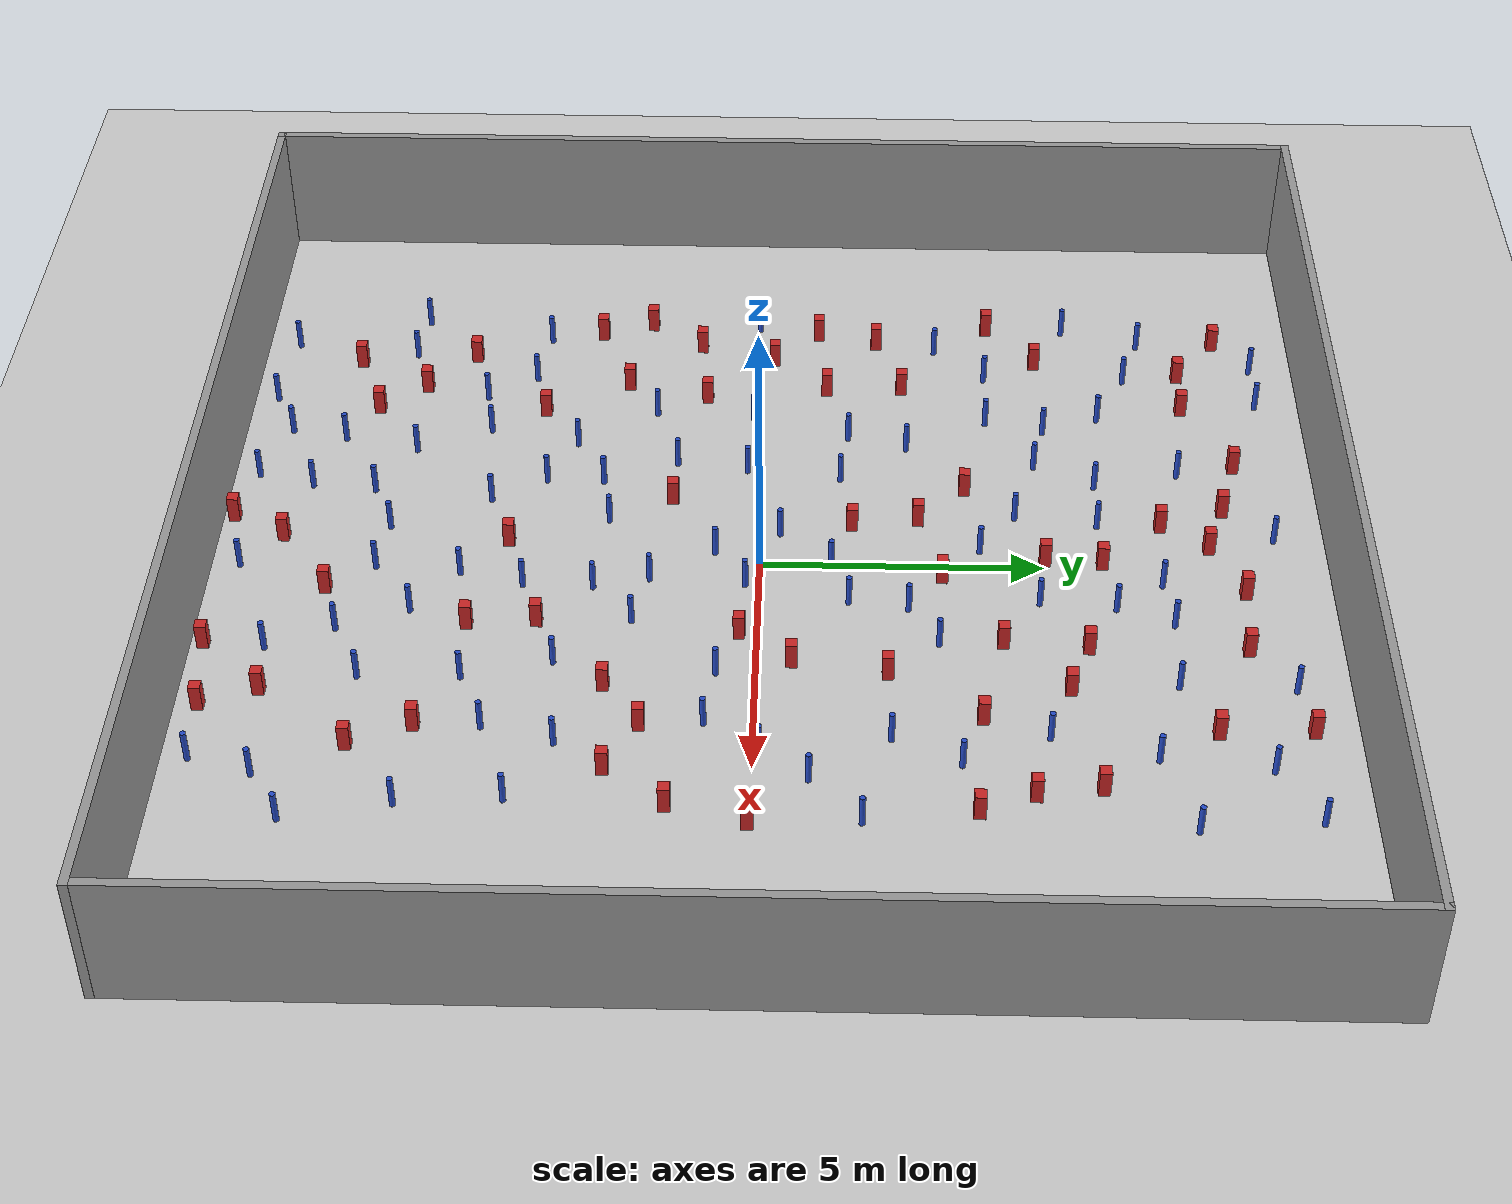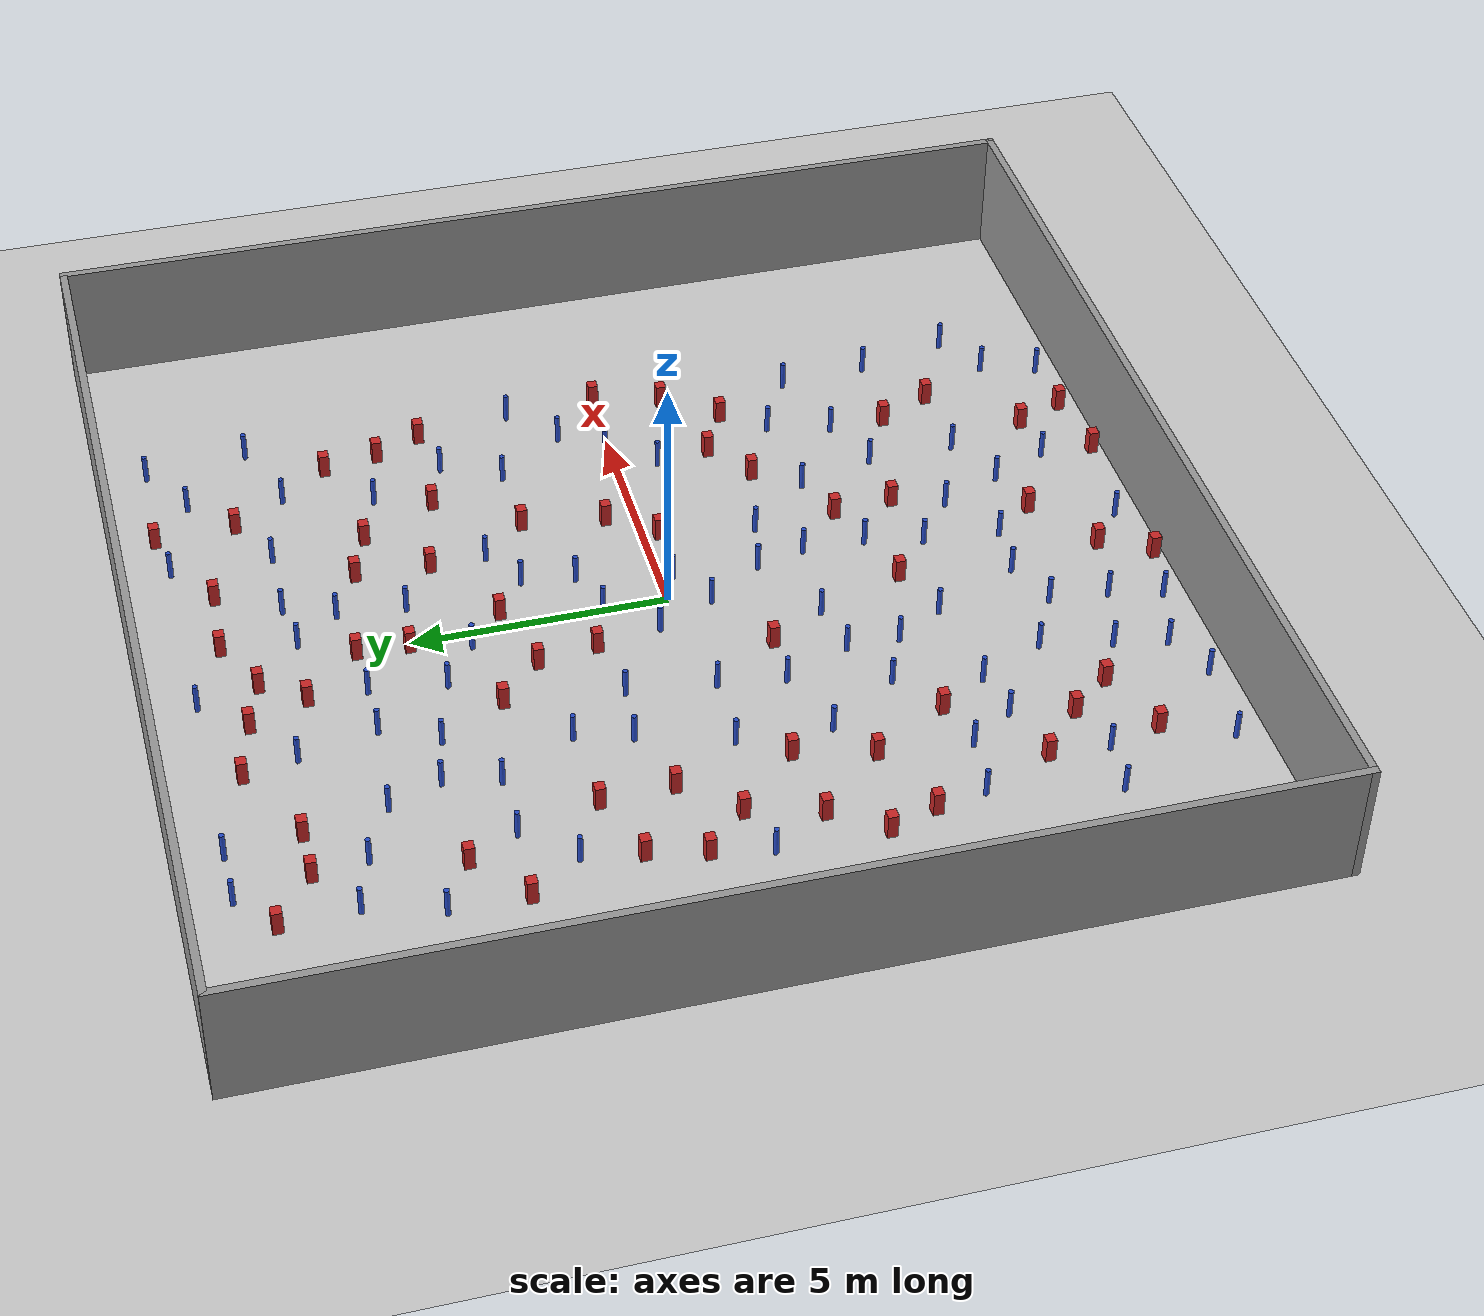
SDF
<sdf version="1.6">
 <world name="default">
  <light name="sun" type="directional">
   <pose>0 0 1000 0 -0 0</pose>
   <diffuse>0.8 0.8 0.8 1</diffuse>
   <specular>0.1 0.1 0.1 1</specular>
   <attenuation>
    <range>1000</range>
    <constant>0.9</constant>
    <linear>0.01</linear>
    <quadratic>0.001</quadratic>
   </attenuation>
   <direction>-0.5 0.5 -1</direction>
  </light>
  <model name="ground_plane">
   <static>1</static>
   <link name="link">
    <collision name="collision">
     <geometry><plane><normal>0 0 1</normal><size>100 100</size></plane></geometry>
     <surface><friction><ode><mu>100</mu><mu2>50</mu2></ode></friction></surface>
    </collision>
    <visual name="visual">
     <cast_shadows>0</cast_shadows>
     <geometry><plane><normal>0 0 1</normal><size>100 100</size></plane></geometry>
     <material>
      <ambient>1 1 1 1</ambient>
      <diffuse>0.8 0.8 0.8 1</diffuse>
      <specular>0.01 0.01 0.01 1</specular>
     </material>
    </visual>
   </link>
  </model>
  <gravity>0 0 -9.8</gravity>
  <magnetic_field>6e-06 2.3e-05 -4.2e-05</magnetic_field>
  <atmosphere type="adiabatic"/>
  <physics name="default_physics" default="0" type="ode">
   <max_step_size>0.001</max_step_size>
   <real_time_factor>1</real_time_factor>
   <real_time_update_rate>1000</real_time_update_rate>
  </physics>
  <scene><ambient>0.4 0.4 0.4 1</ambient><background>0.7 0.7 0.7 1</background><shadows>1</shadows></scene>
  <spherical_coordinates>
   <surface_model>EARTH_WGS84</surface_model>
   <latitude_deg>0</latitude_deg>
   <longitude_deg>0</longitude_deg>
   <elevation>0</elevation>
   <heading_deg>0</heading_deg>
  </spherical_coordinates>
  <plugin name="gazebo_occupancy_map" filename="libgazebo_2Dmap_plugin.so">
   <map_resolution>0.05</map_resolution>
   <map_topic>generated_map</map_topic>
   <map_height>0.01</map_height>
   <map_size_x>50</map_size_x>
   <map_size_y>50</map_size_y>
  </plugin>
  <model name="NamedLocations">
   <static>1</static>
   <link name="DefaultStart"><pose>8.5 0 0 0 -0 3.14</pose></link>
  </model>
  <model name="20x20_walls">
   <pose>0.044518 0.1761 0 0 -0 0</pose>
   <link name="Wall_1">
    <collision name="Wall_1_Collision">
     <geometry><box><size>20 0.15 2.5</size></box></geometry>
     <pose>0 0 1.25 0 -0 0</pose>
    </collision>
    <visual name="Wall_1_Visual">
     <pose>0 0 1.25 0 -0 0</pose>
     <geometry><box><size>20 0.15 2.5</size></box></geometry>
     <material>
      <script><uri>file://media/materials/scripts/gazebo.material</uri><name>Gazebo/Grey</name></script>
      <ambient>0.976471 0.992157 1 1</ambient>
     </material>
     <meta><layer>0</layer></meta>
    </visual>
    <pose>0 9.925 0 0 -0 0</pose>
   </link>
   <link name="Wall_3">
    <collision name="Wall_3_Collision">
     <geometry><box><size>20 0.15 2.5</size></box></geometry>
     <pose>0 0 1.25 0 -0 0</pose>
    </collision>
    <visual name="Wall_3_Visual">
     <pose>0 0 1.25 0 -0 0</pose>
     <geometry><box><size>20 0.15 2.5</size></box></geometry>
     <material>
      <script><uri>file://media/materials/scripts/gazebo.material</uri><name>Gazebo/Grey</name></script>
      <ambient>0.976471 0.992157 1 1</ambient>
     </material>
     <meta><layer>0</layer></meta>
    </visual>
    <pose>9.925 0 0 0 0 -1.5708</pose>
   </link>
   <link name="Wall_4">
    <collision name="Wall_4_Collision">
     <geometry><box><size>20 0.15 2.5</size></box></geometry>
     <pose>0 0 1.25 0 -0 0</pose>
    </collision>
    <visual name="Wall_4_Visual">
     <pose>0 0 1.25 0 -0 0</pose>
     <geometry><box><size>20 0.15 2.5</size></box></geometry>
     <material>
      <script><uri>file://media/materials/scripts/gazebo.material</uri><name>Gazebo/Grey</name></script>
      <ambient>0.976471 0.992157 1 1</ambient>
     </material>
     <meta><layer>0</layer></meta>
    </visual>
    <pose>0 -9.925 0 0 -0 3.14159</pose>
   </link>
   <link name="Wall_5">
    <collision name="Wall_5_Collision">
     <geometry><box><size>20 0.15 2.5</size></box></geometry>
     <pose>0 0 1.25 0 -0 0</pose>
    </collision>
    <visual name="Wall_5_Visual">
     <pose>0 0 1.25 0 -0 0</pose>
     <geometry><box><size>20 0.15 2.5</size></box></geometry>
     <material>
      <script><uri>file://media/materials/scripts/gazebo.material</uri><name>Gazebo/Grey</name></script>
      <ambient>0.976471 0.992157 1 1</ambient>
     </material>
     <meta><layer>0</layer></meta>
    </visual>
    <pose>-9.925 0 0 0 -0 1.5708</pose>
   </link>
   <static>1</static>
  </model>
  <model name="pole_obstacle0">
   <static>0</static>
   <link name="link">
    <pose>0 0 0.3 0 -0 0</pose>
    <inertial>
     <mass>1</mass>
     <inertia><ixx>0.145833</ixx><ixy>0</ixy><ixz>0</ixz><iyy>0.145833</iyy><iyz>0</iyz><izz>0.125</izz></inertia>
    </inertial>
    <collision name="collision">
     <geometry><cylinder><radius>0.05</radius><length>0.6</length></cylinder></geometry>
    </collision>
    <visual name="visual">
     <geometry><cylinder><radius>0.05</radius><length>0.6</length></cylinder></geometry>
     <material>
      <script><name>Gazebo/Blue</name><uri>file://media/materials/scripts/gazebo.material</uri></script>
     </material>
    </visual>
   </link>
   <pose>-0.847177 -6.63387 -7e-06 0 -0 1e-05</pose>
  </model>
  <model name="pole_obstacle1">
   <static>0</static>
   <link name="link">
    <pose>0 0 0.3 0 -0 0</pose>
    <inertial>
     <mass>1</mass>
     <inertia><ixx>0.145833</ixx><ixy>0</ixy><ixz>0</ixz><iyy>0.145833</iyy><iyz>0</iyz><izz>0.125</izz></inertia>
    </inertial>
    <collision name="collision">
     <geometry><cylinder><radius>0.05</radius><length>0.6</length></cylinder></geometry>
    </collision>
    <visual name="visual">
     <geometry><cylinder><radius>0.05</radius><length>0.6</length></cylinder></geometry>
     <material>
      <script><name>Gazebo/Blue</name><uri>file://media/materials/scripts/gazebo.material</uri></script>
     </material>
    </visual>
   </link>
   <pose>5.36775 -8.12371 -6e-06 0 -0 3e-06</pose>
  </model>
  <model name="square_post_obstacle0">
   <static>0</static>
   <link name="link">
    <pose>0 0 0.25 0 -0 0</pose>
    <inertial>
     <mass>100</mass>
     <inertia>
      <ixx>0.166667</ixx>
      <ixy>0</ixy>
      <ixz>0</ixz>
      <iyy>0.166667</iyy>
      <iyz>0</iyz>
      <izz>0.166667</izz>
     </inertia>
    </inertial>
    <collision name="collision"><geometry><box><size>0.2 0.2 0.5</size></box></geometry></collision>
    <visual name="visual">
     <geometry><box><size>0.2 0.2 0.5</size></box></geometry>
     <material>
      <script><name>Gazebo/Red</name><uri>file://media/materials/scripts/gazebo.material</uri></script>
     </material>
    </visual>
   </link>
   <pose>3.18176 -2.55191 0 -5e-06 -0 0.000241</pose>
  </model>
  <model name="square_post_obstacle1">
   <static>0</static>
   <link name="link">
    <pose>0 0 0.25 0 -0 0</pose>
    <inertial>
     <mass>100</mass>
     <inertia>
      <ixx>0.166667</ixx>
      <ixy>0</ixy>
      <ixz>0</ixz>
      <iyy>0.166667</iyy>
      <iyz>0</iyz>
      <izz>0.166667</izz>
     </inertia>
    </inertial>
    <collision name="collision"><geometry><box><size>0.2 0.2 0.5</size></box></geometry></collision>
    <visual name="visual">
     <geometry><box><size>0.2 0.2 0.5</size></box></geometry>
     <material>
      <script><name>Gazebo/Red</name><uri>file://media/materials/scripts/gazebo.material</uri></script>
     </material>
    </visual>
   </link>
   <pose>-5.89802 0.141279 0 -5e-06 -0 0.000241</pose>
  </model>
  <model name="square_post_obstacle2">
   <static>0</static>
   <link name="link">
    <pose>0 0 0.25 0 -0 0</pose>
    <inertial>
     <mass>100</mass>
     <inertia>
      <ixx>0.166667</ixx>
      <ixy>0</ixy>
      <ixz>0</ixz>
      <iyy>0.166667</iyy>
      <iyz>0</iyz>
      <izz>0.166667</izz>
     </inertia>
    </inertial>
    <collision name="collision"><geometry><box><size>0.2 0.2 0.5</size></box></geometry></collision>
    <visual name="visual">
     <geometry><box><size>0.2 0.2 0.5</size></box></geometry>
     <material>
      <script><name>Gazebo/Red</name><uri>file://media/materials/scripts/gazebo.material</uri></script>
     </material>
    </visual>
   </link>
   <pose>-6.28758 -1.26073 0 -5e-06 -0 0.000241</pose>
  </model>
  <model name="square_post_obstacle3">
   <static>0</static>
   <link name="link">
    <pose>0 0 0.25 0 -0 0</pose>
    <inertial>
     <mass>100</mass>
     <inertia>
      <ixx>0.166667</ixx>
      <ixy>0</ixy>
      <ixz>0</ixz>
      <iyy>0.166667</iyy>
      <iyz>0</iyz>
      <izz>0.166667</izz>
     </inertia>
    </inertial>
    <collision name="collision"><geometry><box><size>0.2 0.2 0.5</size></box></geometry></collision>
    <visual name="visual">
     <geometry><box><size>0.2 0.2 0.5</size></box></geometry>
     <material>
      <script><name>Gazebo/Red</name><uri>file://media/materials/scripts/gazebo.material</uri></script>
     </material>
    </visual>
   </link>
   <pose>-5.67275 -7.77645 0 -5e-06 -0 0.000241</pose>
  </model>
  <model name="pole_obstacle2">
   <static>0</static>
   <link name="link">
    <pose>0 0 0.3 0 -0 0</pose>
    <inertial>
     <mass>1</mass>
     <inertia><ixx>0.145833</ixx><ixy>0</ixy><ixz>0</ixz><iyy>0.145833</iyy><iyz>0</iyz><izz>0.125</izz></inertia>
    </inertial>
    <collision name="collision">
     <geometry><cylinder><radius>0.05</radius><length>0.6</length></cylinder></geometry>
    </collision>
    <visual name="visual">
     <geometry><cylinder><radius>0.05</radius><length>0.6</length></cylinder></geometry>
     <material>
      <script><name>Gazebo/Blue</name><uri>file://media/materials/scripts/gazebo.material</uri></script>
     </material>
    </visual>
   </link>
   <pose>1.06586 6.21019 -1e-06 -0 1e-06 1.1e-05</pose>
  </model>
  <model name="pole_obstacle3">
   <static>0</static>
   <link name="link">
    <pose>0 0 0.3 0 -0 0</pose>
    <inertial>
     <mass>1</mass>
     <inertia><ixx>0.145833</ixx><ixy>0</ixy><ixz>0</ixz><iyy>0.145833</iyy><iyz>0</iyz><izz>0.125</izz></inertia>
    </inertial>
    <collision name="collision">
     <geometry><cylinder><radius>0.05</radius><length>0.6</length></cylinder></geometry>
    </collision>
    <visual name="visual">
     <geometry><cylinder><radius>0.05</radius><length>0.6</length></cylinder></geometry>
     <material>
      <script><name>Gazebo/Blue</name><uri>file://media/materials/scripts/gazebo.material</uri></script>
     </material>
    </visual>
   </link>
   <pose>-4.64776 -5.25846 -1e-06 -0 -1e-06 7e-06</pose>
  </model>
  <model name="pole_obstacle4">
   <static>0</static>
   <link name="link">
    <pose>0 0 0.3 0 -0 0</pose>
    <inertial>
     <mass>1</mass>
     <inertia><ixx>0.145833</ixx><ixy>0</ixy><ixz>0</ixz><iyy>0.145833</iyy><iyz>0</iyz><izz>0.125</izz></inertia>
    </inertial>
    <collision name="collision">
     <geometry><cylinder><radius>0.05</radius><length>0.6</length></cylinder></geometry>
    </collision>
    <visual name="visual">
     <geometry><cylinder><radius>0.05</radius><length>0.6</length></cylinder></geometry>
     <material>
      <script><name>Gazebo/Blue</name><uri>file://media/materials/scripts/gazebo.material</uri></script>
     </material>
    </visual>
   </link>
   <pose>4.92123 8.50647 -6e-06 0 -0 3e-06</pose>
  </model>
  <model name="square_post_obstacle4">
   <static>0</static>
   <link name="link">
    <pose>0 0 0.25 0 -0 0</pose>
    <inertial>
     <mass>100</mass>
     <inertia>
      <ixx>0.166667</ixx>
      <ixy>0</ixy>
      <ixz>0</ixz>
      <iyy>0.166667</iyy>
      <iyz>0</iyz>
      <izz>0.166667</izz>
     </inertia>
    </inertial>
    <collision name="collision"><geometry><box><size>0.2 0.2 0.5</size></box></geometry></collision>
    <visual name="visual">
     <geometry><box><size>0.2 0.2 0.5</size></box></geometry>
     <material>
      <script><name>Gazebo/Red</name><uri>file://media/materials/scripts/gazebo.material</uri></script>
     </material>
    </visual>
   </link>
   <pose>-4.25915 -7.26195 0 -5e-06 -0 0.000241</pose>
  </model>
  <model name="pole_obstacle5">
   <static>0</static>
   <link name="link">
    <pose>0 0 0.3 0 -0 0</pose>
    <inertial>
     <mass>1</mass>
     <inertia><ixx>0.145833</ixx><ixy>0</ixy><ixz>0</ixz><iyy>0.145833</iyy><iyz>0</iyz><izz>0.125</izz></inertia>
    </inertial>
    <collision name="collision">
     <geometry><cylinder><radius>0.05</radius><length>0.6</length></cylinder></geometry>
    </collision>
    <visual name="visual">
     <geometry><cylinder><radius>0.05</radius><length>0.6</length></cylinder></geometry>
     <material>
      <script><name>Gazebo/Blue</name><uri>file://media/materials/scripts/gazebo.material</uri></script>
     </material>
    </visual>
   </link>
   <pose>-1.13885 6.0064 -1e-06 -0 1e-06 1.1e-05</pose>
  </model>
  <model name="pole_obstacle6">
   <static>0</static>
   <link name="link">
    <pose>0 0 0.3 0 -0 0</pose>
    <inertial>
     <mass>1</mass>
     <inertia><ixx>0.145833</ixx><ixy>0</ixy><ixz>0</ixz><iyy>0.145833</iyy><iyz>0</iyz><izz>0.125</izz></inertia>
    </inertial>
    <collision name="collision">
     <geometry><cylinder><radius>0.05</radius><length>0.6</length></cylinder></geometry>
    </collision>
    <visual name="visual">
     <geometry><cylinder><radius>0.05</radius><length>0.6</length></cylinder></geometry>
     <material>
      <script><name>Gazebo/Blue</name><uri>file://media/materials/scripts/gazebo.material</uri></script>
     </material>
    </visual>
   </link>
   <pose>-3.5662 1.5504 -6e-06 1e-06 -1e-06 8e-06</pose>
  </model>
  <model name="square_post_obstacle5">
   <static>0</static>
   <link name="link">
    <pose>0 0 0.25 0 -0 0</pose>
    <inertial>
     <mass>100</mass>
     <inertia>
      <ixx>0.166667</ixx>
      <ixy>0</ixy>
      <ixz>0</ixz>
      <iyy>0.166667</iyy>
      <iyz>0</iyz>
      <izz>0.166667</izz>
     </inertia>
    </inertial>
    <collision name="collision"><geometry><box><size>0.2 0.2 0.5</size></box></geometry></collision>
    <visual name="visual">
     <geometry><box><size>0.2 0.2 0.5</size></box></geometry>
     <material>
      <script><name>Gazebo/Red</name><uri>file://media/materials/scripts/gazebo.material</uri></script>
     </material>
    </visual>
   </link>
   <pose>5.13936 -2.42445 0 -5e-06 -0 0.000241</pose>
  </model>
  <model name="square_post_obstacle6">
   <static>0</static>
   <link name="link">
    <pose>0 0 0.25 0 -0 0</pose>
    <inertial>
     <mass>100</mass>
     <inertia>
      <ixx>0.166667</ixx>
      <ixy>0</ixy>
      <ixz>0</ixz>
      <iyy>0.166667</iyy>
      <iyz>0</iyz>
      <izz>0.166667</izz>
     </inertia>
    </inertial>
    <collision name="collision"><geometry><box><size>0.2 0.2 0.5</size></box></geometry></collision>
    <visual name="visual">
     <geometry><box><size>0.2 0.2 0.5</size></box></geometry>
     <material>
      <script><name>Gazebo/Red</name><uri>file://media/materials/scripts/gazebo.material</uri></script>
     </material>
    </visual>
   </link>
   <pose>3.40714 -8.30701 0 -5e-06 -0 0.000241</pose>
  </model>
  <model name="square_post_obstacle7">
   <static>0</static>
   <link name="link">
    <pose>0 0 0.25 0 -0 0</pose>
    <inertial>
     <mass>100</mass>
     <inertia>
      <ixx>0.166667</ixx>
      <ixy>0</ixy>
      <ixz>0</ixz>
      <iyy>0.166667</iyy>
      <iyz>0</iyz>
      <izz>0.166667</izz>
     </inertia>
    </inertial>
    <collision name="collision"><geometry><box><size>0.2 0.2 0.5</size></box></geometry></collision>
    <visual name="visual">
     <geometry><box><size>0.2 0.2 0.5</size></box></geometry>
     <material>
      <script><name>Gazebo/Red</name><uri>file://media/materials/scripts/gazebo.material</uri></script>
     </material>
    </visual>
   </link>
   <pose>-5.86758 -5.58678 0 -5e-06 -0 0.000241</pose>
  </model>
  <model name="square_post_obstacle8">
   <static>0</static>
   <link name="link">
    <pose>0 0 0.25 0 -0 0</pose>
    <inertial>
     <mass>100</mass>
     <inertia>
      <ixx>0.166667</ixx>
      <ixy>0</ixy>
      <ixz>0</ixz>
      <iyy>0.166667</iyy>
      <iyz>0</iyz>
      <izz>0.166667</izz>
     </inertia>
    </inertial>
    <collision name="collision"><geometry><box><size>0.2 0.2 0.5</size></box></geometry></collision>
    <visual name="visual">
     <geometry><box><size>0.2 0.2 0.5</size></box></geometry>
     <material>
      <script><name>Gazebo/Red</name><uri>file://media/materials/scripts/gazebo.material</uri></script>
     </material>
    </visual>
   </link>
   <pose>5.9276 -1.37575 0 -5e-06 -0 0.000241</pose>
  </model>
  <model name="square_post_obstacle9">
   <static>0</static>
   <link name="link">
    <pose>0 0 0.25 0 -0 0</pose>
    <inertial>
     <mass>100</mass>
     <inertia>
      <ixx>0.166667</ixx>
      <ixy>0</ixy>
      <ixz>0</ixz>
      <iyy>0.166667</iyy>
      <iyz>0</iyz>
      <izz>0.166667</izz>
     </inertia>
    </inertial>
    <collision name="collision"><geometry><box><size>0.2 0.2 0.5</size></box></geometry></collision>
    <visual name="visual">
     <geometry><box><size>0.2 0.2 0.5</size></box></geometry>
     <material>
      <script><name>Gazebo/Red</name><uri>file://media/materials/scripts/gazebo.material</uri></script>
     </material>
    </visual>
   </link>
   <pose>-1.0312 1.62568 0 -5e-06 -0 0.000241</pose>
  </model>
  <model name="square_post_obstacle10">
   <static>0</static>
   <link name="link">
    <pose>0 0 0.25 0 -0 0</pose>
    <inertial>
     <mass>100</mass>
     <inertia>
      <ixx>0.166667</ixx>
      <ixy>0</ixy>
      <ixz>0</ixz>
      <iyy>0.166667</iyy>
      <iyz>0</iyz>
      <izz>0.166667</izz>
     </inertia>
    </inertial>
    <collision name="collision"><geometry><box><size>0.2 0.2 0.5</size></box></geometry></collision>
    <visual name="visual">
     <geometry><box><size>0.2 0.2 0.5</size></box></geometry>
     <material>
      <script><name>Gazebo/Red</name><uri>file://media/materials/scripts/gazebo.material</uri></script>
     </material>
    </visual>
   </link>
   <pose>1.6105 -3.80443 0 -5e-06 -0 0.000241</pose>
  </model>
  <model name="pole_obstacle7">
   <static>0</static>
   <link name="link">
    <pose>0 0 0.3 0 -0 0</pose>
    <inertial>
     <mass>1</mass>
     <inertia><ixx>0.145833</ixx><ixy>0</ixy><ixz>0</ixz><iyy>0.145833</iyy><iyz>0</iyz><izz>0.125</izz></inertia>
    </inertial>
    <collision name="collision">
     <geometry><cylinder><radius>0.05</radius><length>0.6</length></cylinder></geometry>
    </collision>
    <visual name="visual">
     <geometry><cylinder><radius>0.05</radius><length>0.6</length></cylinder></geometry>
     <material>
      <script><name>Gazebo/Blue</name><uri>file://media/materials/scripts/gazebo.material</uri></script>
     </material>
    </visual>
   </link>
   <pose>-2.36217 1.41405 -1e-06 -0 1e-06 1.1e-05</pose>
  </model>
  <model name="pole_obstacle8">
   <static>0</static>
   <link name="link">
    <pose>0 0 0.3 0 -0 0</pose>
    <inertial>
     <mass>1</mass>
     <inertia><ixx>0.145833</ixx><ixy>0</ixy><ixz>0</ixz><iyy>0.145833</iyy><iyz>0</iyz><izz>0.125</izz></inertia>
    </inertial>
    <collision name="collision">
     <geometry><cylinder><radius>0.05</radius><length>0.6</length></cylinder></geometry>
    </collision>
    <visual name="visual">
     <geometry><cylinder><radius>0.05</radius><length>0.6</length></cylinder></geometry>
     <material>
      <script><name>Gazebo/Blue</name><uri>file://media/materials/scripts/gazebo.material</uri></script>
     </material>
    </visual>
   </link>
   <pose>2.97873 7.12761 -2e-06 -1e-06 -0 9e-06</pose>
  </model>
  <model name="pole_obstacle9">
   <static>0</static>
   <link name="link">
    <pose>0 0 0.3 0 -0 0</pose>
    <inertial>
     <mass>1</mass>
     <inertia><ixx>0.145833</ixx><ixy>0</ixy><ixz>0</ixz><iyy>0.145833</iyy><iyz>0</iyz><izz>0.125</izz></inertia>
    </inertial>
    <collision name="collision">
     <geometry><cylinder><radius>0.05</radius><length>0.6</length></cylinder></geometry>
    </collision>
    <visual name="visual">
     <geometry><cylinder><radius>0.05</radius><length>0.6</length></cylinder></geometry>
     <material>
      <script><name>Gazebo/Blue</name><uri>file://media/materials/scripts/gazebo.material</uri></script>
     </material>
    </visual>
   </link>
   <pose>0.944334 4.88568 -1e-06 -1e-06 -0 1.3e-05</pose>
  </model>
  <model name="pole_obstacle10">
   <static>0</static>
   <link name="link">
    <pose>0 0 0.3 0 -0 0</pose>
    <inertial>
     <mass>1</mass>
     <inertia><ixx>0.145833</ixx><ixy>0</ixy><ixz>0</ixz><iyy>0.145833</iyy><iyz>0</iyz><izz>0.125</izz></inertia>
    </inertial>
    <collision name="collision">
     <geometry><cylinder><radius>0.05</radius><length>0.6</length></cylinder></geometry>
    </collision>
    <visual name="visual">
     <geometry><cylinder><radius>0.05</radius><length>0.6</length></cylinder></geometry>
     <material>
      <script><name>Gazebo/Blue</name><uri>file://media/materials/scripts/gazebo.material</uri></script>
     </material>
    </visual>
   </link>
   <pose>-4.11229 -0.209701 -2e-06 -1e-06 -0 9e-06</pose>
  </model>
  <model name="pole_obstacle11">
   <static>0</static>
   <link name="link">
    <pose>0 0 0.3 0 -0 0</pose>
    <inertial>
     <mass>1</mass>
     <inertia><ixx>0.145833</ixx><ixy>0</ixy><ixz>0</ixz><iyy>0.145833</iyy><iyz>0</iyz><izz>0.125</izz></inertia>
    </inertial>
    <collision name="collision">
     <geometry><cylinder><radius>0.05</radius><length>0.6</length></cylinder></geometry>
    </collision>
    <visual name="visual">
     <geometry><cylinder><radius>0.05</radius><length>0.6</length></cylinder></geometry>
     <material>
      <script><name>Gazebo/Blue</name><uri>file://media/materials/scripts/gazebo.material</uri></script>
     </material>
    </visual>
   </link>
   <pose>-6.25506 3.1961 -8e-06 0 -0 1.2e-05</pose>
  </model>
  <model name="pole_obstacle12">
   <static>0</static>
   <link name="link">
    <pose>0 0 0.3 0 -0 0</pose>
    <inertial>
     <mass>1</mass>
     <inertia><ixx>0.145833</ixx><ixy>0</ixy><ixz>0</ixz><iyy>0.145833</iyy><iyz>0</iyz><izz>0.125</izz></inertia>
    </inertial>
    <collision name="collision">
     <geometry><cylinder><radius>0.05</radius><length>0.6</length></cylinder></geometry>
    </collision>
    <visual name="visual">
     <geometry><cylinder><radius>0.05</radius><length>0.6</length></cylinder></geometry>
     <material>
      <script><name>Gazebo/Blue</name><uri>file://media/materials/scripts/gazebo.material</uri></script>
     </material>
    </visual>
   </link>
   <pose>6.21061 1.79303 -1e-06 -0 1e-06 1.1e-05</pose>
  </model>
  <model name="pole_obstacle13">
   <static>0</static>
   <link name="link">
    <pose>0 0 0.3 0 -0 0</pose>
    <inertial>
     <mass>1</mass>
     <inertia><ixx>0.145833</ixx><ixy>0</ixy><ixz>0</ixz><iyy>0.145833</iyy><iyz>0</iyz><izz>0.125</izz></inertia>
    </inertial>
    <collision name="collision">
     <geometry><cylinder><radius>0.05</radius><length>0.6</length></cylinder></geometry>
    </collision>
    <visual name="visual">
     <geometry><cylinder><radius>0.05</radius><length>0.6</length></cylinder></geometry>
     <material>
      <script><name>Gazebo/Blue</name><uri>file://media/materials/scripts/gazebo.material</uri></script>
     </material>
    </visual>
   </link>
   <pose>4.01801 -0.832099 -3e-06 0 -0 1e-05</pose>
  </model>
  <model name="pole_obstacle14">
   <static>0</static>
   <link name="link">
    <pose>0 0 0.3 0 -0 0</pose>
    <inertial>
     <mass>1</mass>
     <inertia><ixx>0.145833</ixx><ixy>0</ixy><ixz>0</ixz><iyy>0.145833</iyy><iyz>0</iyz><izz>0.125</izz></inertia>
    </inertial>
    <collision name="collision">
     <geometry><cylinder><radius>0.05</radius><length>0.6</length></cylinder></geometry>
    </collision>
    <visual name="visual">
     <geometry><cylinder><radius>0.05</radius><length>0.6</length></cylinder></geometry>
     <material>
      <script><name>Gazebo/Blue</name><uri>file://media/materials/scripts/gazebo.material</uri></script>
     </material>
    </visual>
   </link>
   <pose>2.00787 3.11889 -1e-06 -1e-06 -1e-06 1.3e-05</pose>
  </model>
  <model name="square_post_obstacle11">
   <static>0</static>
   <link name="link">
    <pose>0 0 0.25 0 -0 0</pose>
    <inertial>
     <mass>100</mass>
     <inertia>
      <ixx>0.166667</ixx>
      <ixy>0</ixy>
      <ixz>0</ixz>
      <iyy>0.166667</iyy>
      <iyz>0</iyz>
      <izz>0.166667</izz>
     </inertia>
    </inertial>
    <collision name="collision"><geometry><box><size>0.2 0.2 0.5</size></box></geometry></collision>
    <visual name="visual">
     <geometry><box><size>0.2 0.2 0.5</size></box></geometry>
     <material>
      <script><name>Gazebo/Red</name><uri>file://media/materials/scripts/gazebo.material</uri></script>
     </material>
    </visual>
   </link>
   <pose>0.330037 3.2044 0 -5e-06 -0 0.000241</pose>
  </model>
  <model name="square_post_obstacle12">
   <static>0</static>
   <link name="link">
    <pose>0 0 0.25 0 -0 0</pose>
    <inertial>
     <mass>100</mass>
     <inertia>
      <ixx>0.166667</ixx>
      <ixy>0</ixy>
      <ixz>0</ixz>
      <iyy>0.166667</iyy>
      <iyz>0</iyz>
      <izz>0.166667</izz>
     </inertia>
    </inertial>
    <collision name="collision"><geometry><box><size>0.2 0.2 0.5</size></box></geometry></collision>
    <visual name="visual">
     <geometry><box><size>0.2 0.2 0.5</size></box></geometry>
     <material>
      <script><name>Gazebo/Red</name><uri>file://media/materials/scripts/gazebo.material</uri></script>
     </material>
    </visual>
   </link>
   <pose>-5.87987 5.09643 0 -5e-06 -0 0.000241</pose>
  </model>
  <model name="pole_obstacle15">
   <static>0</static>
   <link name="link">
    <pose>0 0 0.3 0 -0 0</pose>
    <inertial>
     <mass>1</mass>
     <inertia><ixx>0.145833</ixx><ixy>0</ixy><ixz>0</ixz><iyy>0.145833</iyy><iyz>0</iyz><izz>0.125</izz></inertia>
    </inertial>
    <collision name="collision">
     <geometry><cylinder><radius>0.05</radius><length>0.6</length></cylinder></geometry>
    </collision>
    <visual name="visual">
     <geometry><cylinder><radius>0.05</radius><length>0.6</length></cylinder></geometry>
     <material>
      <script><name>Gazebo/Blue</name><uri>file://media/materials/scripts/gazebo.material</uri></script>
     </material>
    </visual>
   </link>
   <pose>0.428044 7.05702 -9e-06 1e-06 -1e-06 1.1e-05</pose>
  </model>
  <model name="square_post_obstacle13">
   <static>0</static>
   <link name="link">
    <pose>0 0 0.25 0 -0 0</pose>
    <inertial>
     <mass>100</mass>
     <inertia>
      <ixx>0.166667</ixx>
      <ixy>0</ixy>
      <ixz>0</ixz>
      <iyy>0.166667</iyy>
      <iyz>0</iyz>
      <izz>0.166667</izz>
     </inertia>
    </inertial>
    <collision name="collision"><geometry><box><size>0.2 0.2 0.5</size></box></geometry></collision>
    <visual name="visual">
     <geometry><box><size>0.2 0.2 0.5</size></box></geometry>
     <material>
      <script><name>Gazebo/Red</name><uri>file://media/materials/scripts/gazebo.material</uri></script>
     </material>
    </visual>
   </link>
   <pose>-1.71 -1.60937 0 -5e-06 -0 0.000241</pose>
  </model>
  <model name="pole_obstacle16">
   <static>0</static>
   <link name="link">
    <pose>0 0 0.3 0 -0 0</pose>
    <inertial>
     <mass>1</mass>
     <inertia><ixx>0.145833</ixx><ixy>0</ixy><ixz>0</ixz><iyy>0.145833</iyy><iyz>0</iyz><izz>0.125</izz></inertia>
    </inertial>
    <collision name="collision">
     <geometry><cylinder><radius>0.05</radius><length>0.6</length></cylinder></geometry>
    </collision>
    <visual name="visual">
     <geometry><cylinder><radius>0.05</radius><length>0.6</length></cylinder></geometry>
     <material>
      <script><name>Gazebo/Blue</name><uri>file://media/materials/scripts/gazebo.material</uri></script>
     </material>
    </visual>
   </link>
   <pose>-3.65186 -5.09282 -2e-06 -1e-06 -0 1.1e-05</pose>
  </model>
  <model name="pole_obstacle17">
   <static>0</static>
   <link name="link">
    <pose>0 0 0.3 0 -0 0</pose>
    <inertial>
     <mass>1</mass>
     <inertia><ixx>0.145833</ixx><ixy>0</ixy><ixz>0</ixz><iyy>0.145833</iyy><iyz>0</iyz><izz>0.125</izz></inertia>
    </inertial>
    <collision name="collision">
     <geometry><cylinder><radius>0.05</radius><length>0.6</length></cylinder></geometry>
    </collision>
    <visual name="visual">
     <geometry><cylinder><radius>0.05</radius><length>0.6</length></cylinder></geometry>
     <material>
      <script><name>Gazebo/Blue</name><uri>file://media/materials/scripts/gazebo.material</uri></script>
     </material>
    </visual>
   </link>
   <pose>-2.56661 -0.285708 -7e-06 0 -0 8e-06</pose>
  </model>
  <model name="pole_obstacle18">
   <static>0</static>
   <link name="link">
    <pose>0 0 0.3 0 -0 0</pose>
    <inertial>
     <mass>1</mass>
     <inertia><ixx>0.145833</ixx><ixy>0</ixy><ixz>0</ixz><iyy>0.145833</iyy><iyz>0</iyz><izz>0.125</izz></inertia>
    </inertial>
    <collision name="collision">
     <geometry><cylinder><radius>0.05</radius><length>0.6</length></cylinder></geometry>
    </collision>
    <visual name="visual">
     <geometry><cylinder><radius>0.05</radius><length>0.6</length></cylinder></geometry>
     <material>
      <script><name>Gazebo/Blue</name><uri>file://media/materials/scripts/gazebo.material</uri></script>
     </material>
    </visual>
   </link>
   <pose>4.19335 -4.50781 -1e-06 -0 -1e-06 7e-06</pose>
  </model>
  <model name="pole_obstacle19">
   <static>0</static>
   <link name="link">
    <pose>0 0 0.3 0 -0 0</pose>
    <inertial>
     <mass>1</mass>
     <inertia><ixx>0.145833</ixx><ixy>0</ixy><ixz>0</ixz><iyy>0.145833</iyy><iyz>0</iyz><izz>0.125</izz></inertia>
    </inertial>
    <collision name="collision">
     <geometry><cylinder><radius>0.05</radius><length>0.6</length></cylinder></geometry>
    </collision>
    <visual name="visual">
     <geometry><cylinder><radius>0.05</radius><length>0.6</length></cylinder></geometry>
     <material>
      <script><name>Gazebo/Blue</name><uri>file://media/materials/scripts/gazebo.material</uri></script>
     </material>
    </visual>
   </link>
   <pose>0.015818 1.26048 -7e-06 1e-06 -1e-06 4e-06</pose>
  </model>
  <model name="square_post_obstacle14">
   <static>0</static>
   <link name="link">
    <pose>0 0 0.25 0 -0 0</pose>
    <inertial>
     <mass>100</mass>
     <inertia>
      <ixx>0.166667</ixx>
      <ixy>0</ixy>
      <ixz>0</ixz>
      <iyy>0.166667</iyy>
      <iyz>0</iyz>
      <izz>0.166667</izz>
     </inertia>
    </inertial>
    <collision name="collision"><geometry><box><size>0.2 0.2 0.5</size></box></geometry></collision>
    <visual name="visual">
     <geometry><box><size>0.2 0.2 0.5</size></box></geometry>
     <material>
      <script><name>Gazebo/Red</name><uri>file://media/materials/scripts/gazebo.material</uri></script>
     </material>
    </visual>
   </link>
   <pose>2.79434 2.23426 0 -5e-06 -0 0.000241</pose>
  </model>
  <model name="pole_obstacle20">
   <static>0</static>
   <link name="link">
    <pose>0 0 0.3 0 -0 0</pose>
    <inertial>
     <mass>1</mass>
     <inertia><ixx>0.145833</ixx><ixy>0</ixy><ixz>0</ixz><iyy>0.145833</iyy><iyz>0</iyz><izz>0.125</izz></inertia>
    </inertial>
    <collision name="collision">
     <geometry><cylinder><radius>0.05</radius><length>0.6</length></cylinder></geometry>
    </collision>
    <visual name="visual">
     <geometry><cylinder><radius>0.05</radius><length>0.6</length></cylinder></geometry>
     <material>
      <script><name>Gazebo/Blue</name><uri>file://media/materials/scripts/gazebo.material</uri></script>
     </material>
    </visual>
   </link>
   <pose>0.455199 -1.9194 -2e-06 0 -0 5e-06</pose>
  </model>
  <model name="square_post_obstacle15">
   <static>0</static>
   <link name="link">
    <pose>0 0 0.25 0 -0 0</pose>
    <inertial>
     <mass>100</mass>
     <inertia>
      <ixx>0.166667</ixx>
      <ixy>0</ixy>
      <ixz>0</ixz>
      <iyy>0.166667</iyy>
      <iyz>0</iyz>
      <izz>0.166667</izz>
     </inertia>
    </inertial>
    <collision name="collision"><geometry><box><size>0.2 0.2 0.5</size></box></geometry></collision>
    <visual name="visual">
     <geometry><box><size>0.2 0.2 0.5</size></box></geometry>
     <material>
      <script><name>Gazebo/Red</name><uri>file://media/materials/scripts/gazebo.material</uri></script>
     </material>
    </visual>
   </link>
   <pose>-5.0328 2.5515 0 -5e-06 -0 0.000241</pose>
  </model>
  <model name="pole_obstacle21">
   <static>0</static>
   <link name="link">
    <pose>0 0 0.3 0 -0 0</pose>
    <inertial>
     <mass>1</mass>
     <inertia><ixx>0.145833</ixx><ixy>0</ixy><ixz>0</ixz><iyy>0.145833</iyy><iyz>0</iyz><izz>0.125</izz></inertia>
    </inertial>
    <collision name="collision">
     <geometry><cylinder><radius>0.05</radius><length>0.6</length></cylinder></geometry>
    </collision>
    <visual name="visual">
     <geometry><cylinder><radius>0.05</radius><length>0.6</length></cylinder></geometry>
     <material>
      <script><name>Gazebo/Blue</name><uri>file://media/materials/scripts/gazebo.material</uri></script>
     </material>
    </visual>
   </link>
   <pose>-3.0335 -6.41624 -2e-06 -1e-06 -0 1.1e-05</pose>
  </model>
  <model name="square_post_obstacle16">
   <static>0</static>
   <link name="link">
    <pose>0 0 0.25 0 -0 0</pose>
    <inertial>
     <mass>100</mass>
     <inertia>
      <ixx>0.166667</ixx>
      <ixy>0</ixy>
      <ixz>0</ixz>
      <iyy>0.166667</iyy>
      <iyz>0</iyz>
      <izz>0.166667</izz>
     </inertia>
    </inertial>
    <collision name="collision"><geometry><box><size>0.2 0.2 0.5</size></box></geometry></collision>
    <visual name="visual">
     <geometry><box><size>0.2 0.2 0.5</size></box></geometry>
     <material>
      <script><name>Gazebo/Red</name><uri>file://media/materials/scripts/gazebo.material</uri></script>
     </material>
    </visual>
   </link>
   <pose>-0.538981 -8.50106 0 -5e-06 -0 0.000241</pose>
  </model>
  <model name="pole_obstacle22">
   <static>0</static>
   <link name="link">
    <pose>0 0 0.3 0 -0 0</pose>
    <inertial>
     <mass>1</mass>
     <inertia><ixx>0.145833</ixx><ixy>0</ixy><ixz>0</ixz><iyy>0.145833</iyy><iyz>0</iyz><izz>0.125</izz></inertia>
    </inertial>
    <collision name="collision">
     <geometry><cylinder><radius>0.05</radius><length>0.6</length></cylinder></geometry>
    </collision>
    <visual name="visual">
     <geometry><cylinder><radius>0.05</radius><length>0.6</length></cylinder></geometry>
     <material>
      <script><name>Gazebo/Blue</name><uri>file://media/materials/scripts/gazebo.material</uri></script>
     </material>
    </visual>
   </link>
   <pose>-6.99557 -6.62597 -1e-06 -0 -1e-06 7e-06</pose>
  </model>
  <model name="square_post_obstacle17">
   <static>0</static>
   <link name="link">
    <pose>0 0 0.25 0 -0 0</pose>
    <inertial>
     <mass>100</mass>
     <inertia>
      <ixx>0.166667</ixx>
      <ixy>0</ixy>
      <ixz>0</ixz>
      <iyy>0.166667</iyy>
      <iyz>0</iyz>
      <izz>0.166667</izz>
     </inertia>
    </inertial>
    <collision name="collision"><geometry><box><size>0.2 0.2 0.5</size></box></geometry></collision>
    <visual name="visual">
     <geometry><box><size>0.2 0.2 0.5</size></box></geometry>
     <material>
      <script><name>Gazebo/Red</name><uri>file://media/materials/scripts/gazebo.material</uri></script>
     </material>
    </visual>
   </link>
   <pose>-5.07218 -2.59141 0 -5e-06 -0 0.000241</pose>
  </model>
  <model name="pole_obstacle23">
   <static>0</static>
   <link name="link">
    <pose>0 0 0.3 0 -0 0</pose>
    <inertial>
     <mass>1</mass>
     <inertia><ixx>0.145833</ixx><ixy>0</ixy><ixz>0</ixz><iyy>0.145833</iyy><iyz>0</iyz><izz>0.125</izz></inertia>
    </inertial>
    <collision name="collision">
     <geometry><cylinder><radius>0.05</radius><length>0.6</length></cylinder></geometry>
    </collision>
    <visual name="visual">
     <geometry><cylinder><radius>0.05</radius><length>0.6</length></cylinder></geometry>
     <material>
      <script><name>Gazebo/Blue</name><uri>file://media/materials/scripts/gazebo.material</uri></script>
     </material>
    </visual>
   </link>
   <pose>-6.51548 7.11232 -4e-06 0 -0 1e-06</pose>
  </model>
  <model name="square_post_obstacle18">
   <static>0</static>
   <link name="link">
    <pose>0 0 0.25 0 -0 0</pose>
    <inertial>
     <mass>100</mass>
     <inertia>
      <ixx>0.166667</ixx>
      <ixy>0</ixy>
      <ixz>0</ixz>
      <iyy>0.166667</iyy>
      <iyz>0</iyz>
      <izz>0.166667</izz>
     </inertia>
    </inertial>
    <collision name="collision"><geometry><box><size>0.2 0.2 0.5</size></box></geometry></collision>
    <visual name="visual">
     <geometry><box><size>0.2 0.2 0.5</size></box></geometry>
     <material>
      <script><name>Gazebo/Red</name><uri>file://media/materials/scripts/gazebo.material</uri></script>
     </material>
    </visual>
   </link>
   <pose>4.66731 -6.67754 0 -5e-06 -0 0.000241</pose>
  </model>
  <model name="pole_obstacle24">
   <static>0</static>
   <link name="link">
    <pose>0 0 0.3 0 -0 0</pose>
    <inertial>
     <mass>1</mass>
     <inertia><ixx>0.145833</ixx><ixy>0</ixy><ixz>0</ixz><iyy>0.145833</iyy><iyz>0</iyz><izz>0.125</izz></inertia>
    </inertial>
    <collision name="collision">
     <geometry><cylinder><radius>0.05</radius><length>0.6</length></cylinder></geometry>
    </collision>
    <visual name="visual">
     <geometry><cylinder><radius>0.05</radius><length>0.6</length></cylinder></geometry>
     <material>
      <script><name>Gazebo/Blue</name><uri>file://media/materials/scripts/gazebo.material</uri></script>
     </material>
    </visual>
   </link>
   <pose>-2.2071 -2.8996 -1e-06 1e-06 -1e-06 1e-05</pose>
  </model>
  <model name="square_post_obstacle19">
   <static>0</static>
   <link name="link">
    <pose>0 0 0.25 0 -0 0</pose>
    <inertial>
     <mass>100</mass>
     <inertia>
      <ixx>0.166667</ixx>
      <ixy>0</ixy>
      <ixz>0</ixz>
      <iyy>0.166667</iyy>
      <iyz>0</iyz>
      <izz>0.166667</izz>
     </inertia>
    </inertial>
    <collision name="collision"><geometry><box><size>0.2 0.2 0.5</size></box></geometry></collision>
    <visual name="visual">
     <geometry><box><size>0.2 0.2 0.5</size></box></geometry>
     <material>
      <script><name>Gazebo/Red</name><uri>file://media/materials/scripts/gazebo.material</uri></script>
     </material>
    </visual>
   </link>
   <pose>1.8538 -0.307142 0 -5e-06 -0 0.000241</pose>
  </model>
  <model name="square_post_obstacle20">
   <static>0</static>
   <link name="link">
    <pose>0 0 0.25 0 -0 0</pose>
    <inertial>
     <mass>100</mass>
     <inertia>
      <ixx>0.166667</ixx>
      <ixy>0</ixy>
      <ixz>0</ixz>
      <iyy>0.166667</iyy>
      <iyz>0</iyz>
      <izz>0.166667</izz>
     </inertia>
    </inertial>
    <collision name="collision"><geometry><box><size>0.2 0.2 0.5</size></box></geometry></collision>
    <visual name="visual">
     <geometry><box><size>0.2 0.2 0.5</size></box></geometry>
     <material>
      <script><name>Gazebo/Red</name><uri>file://media/materials/scripts/gazebo.material</uri></script>
     </material>
    </visual>
   </link>
   <pose>-0.489919 -4.46962 0 -5e-06 -0 0.000241</pose>
  </model>
  <model name="square_post_obstacle21">
   <static>0</static>
   <link name="link">
    <pose>0 0 0.25 0 -0 0</pose>
    <inertial>
     <mass>100</mass>
     <inertia>
      <ixx>0.166667</ixx>
      <ixy>0</ixy>
      <ixz>0</ixz>
      <iyy>0.166667</iyy>
      <iyz>0</iyz>
      <izz>0.166667</izz>
     </inertia>
    </inertial>
    <collision name="collision"><geometry><box><size>0.2 0.2 0.5</size></box></geometry></collision>
    <visual name="visual">
     <geometry><box><size>0.2 0.2 0.5</size></box></geometry>
     <material>
      <script><name>Gazebo/Red</name><uri>file://media/materials/scripts/gazebo.material</uri></script>
     </material>
    </visual>
   </link>
   <pose>-6.56118 8.56873 0 -5e-06 -0 0.000241</pose>
  </model>
  <model name="pole_obstacle25">
   <static>0</static>
   <link name="link">
    <pose>0 0 0.3 0 -0 0</pose>
    <inertial>
     <mass>1</mass>
     <inertia><ixx>0.145833</ixx><ixy>0</ixy><ixz>0</ixz><iyy>0.145833</iyy><iyz>0</iyz><izz>0.125</izz></inertia>
    </inertial>
    <collision name="collision">
     <geometry><cylinder><radius>0.05</radius><length>0.6</length></cylinder></geometry>
    </collision>
    <visual name="visual">
     <geometry><cylinder><radius>0.05</radius><length>0.6</length></cylinder></geometry>
     <material>
      <script><name>Gazebo/Blue</name><uri>file://media/materials/scripts/gazebo.material</uri></script>
     </material>
    </visual>
   </link>
   <pose>3.03689 -6.71455 -2e-06 -1e-06 -0 9e-06</pose>
  </model>
  <model name="pole_obstacle26">
   <static>0</static>
   <link name="link">
    <pose>0 0 0.3 0 -0 0</pose>
    <inertial>
     <mass>1</mass>
     <inertia><ixx>0.145833</ixx><ixy>0</ixy><ixz>0</ixz><iyy>0.145833</iyy><iyz>0</iyz><izz>0.125</izz></inertia>
    </inertial>
    <collision name="collision">
     <geometry><cylinder><radius>0.05</radius><length>0.6</length></cylinder></geometry>
    </collision>
    <visual name="visual">
     <geometry><cylinder><radius>0.05</radius><length>0.6</length></cylinder></geometry>
     <material>
      <script><name>Gazebo/Blue</name><uri>file://media/materials/scripts/gazebo.material</uri></script>
     </material>
    </visual>
   </link>
   <pose>3.03408 9.09152 -3e-06 0 -0 9e-06</pose>
  </model>
  <model name="pole_obstacle27">
   <static>0</static>
   <link name="link">
    <pose>0 0 0.3 0 -0 0</pose>
    <inertial>
     <mass>1</mass>
     <inertia><ixx>0.145833</ixx><ixy>0</ixy><ixz>0</ixz><iyy>0.145833</iyy><iyz>0</iyz><izz>0.125</izz></inertia>
    </inertial>
    <collision name="collision">
     <geometry><cylinder><radius>0.05</radius><length>0.6</length></cylinder></geometry>
    </collision>
    <visual name="visual">
     <geometry><cylinder><radius>0.05</radius><length>0.6</length></cylinder></geometry>
     <material>
      <script><name>Gazebo/Blue</name><uri>file://media/materials/scripts/gazebo.material</uri></script>
     </material>
    </visual>
   </link>
   <pose>-3.8262 5.16682 -3e-06 0 -0 7e-06</pose>
  </model>
  <model name="square_post_obstacle22">
   <static>0</static>
   <link name="link">
    <pose>0 0 0.25 0 -0 0</pose>
    <inertial>
     <mass>100</mass>
     <inertia>
      <ixx>0.166667</ixx>
      <ixy>0</ixy>
      <ixz>0</ixz>
      <iyy>0.166667</iyy>
      <iyz>0</iyz>
      <izz>0.166667</izz>
     </inertia>
    </inertial>
    <collision name="collision"><geometry><box><size>0.2 0.2 0.5</size></box></geometry></collision>
    <visual name="visual">
     <geometry><box><size>0.2 0.2 0.5</size></box></geometry>
     <material>
      <script><name>Gazebo/Red</name><uri>file://media/materials/scripts/gazebo.material</uri></script>
     </material>
    </visual>
   </link>
   <pose>3.11926 5.30204 0 -5e-06 -0 0.000241</pose>
  </model>
  <model name="pole_obstacle28">
   <static>0</static>
   <link name="link">
    <pose>0 0 0.3 0 -0 0</pose>
    <inertial>
     <mass>1</mass>
     <inertia><ixx>0.145833</ixx><ixy>0</ixy><ixz>0</ixz><iyy>0.145833</iyy><iyz>0</iyz><izz>0.125</izz></inertia>
    </inertial>
    <collision name="collision">
     <geometry><cylinder><radius>0.05</radius><length>0.6</length></cylinder></geometry>
    </collision>
    <visual name="visual">
     <geometry><cylinder><radius>0.05</radius><length>0.6</length></cylinder></geometry>
     <material>
      <script><name>Gazebo/Blue</name><uri>file://media/materials/scripts/gazebo.material</uri></script>
     </material>
    </visual>
   </link>
   <pose>-6.4692 -4.19105 -1e-06 -0 -1e-06 7e-06</pose>
  </model>
  <model name="square_post_obstacle23">
   <static>0</static>
   <link name="link">
    <pose>0 0 0.25 0 -0 0</pose>
    <inertial>
     <mass>100</mass>
     <inertia>
      <ixx>0.166667</ixx>
      <ixy>0</ixy>
      <ixz>0</ixz>
      <iyy>0.166667</iyy>
      <iyz>0</iyz>
      <izz>0.166667</izz>
     </inertia>
    </inertial>
    <collision name="collision"><geometry><box><size>0.2 0.2 0.5</size></box></geometry></collision>
    <visual name="visual">
     <geometry><box><size>0.2 0.2 0.5</size></box></geometry>
     <material>
      <script><name>Gazebo/Red</name><uri>file://media/materials/scripts/gazebo.material</uri></script>
     </material>
    </visual>
   </link>
   <pose>-2.07569 3.65792 0 -5e-06 -0 0.000241</pose>
  </model>
  <model name="square_post_obstacle24">
   <static>0</static>
   <link name="link">
    <pose>0 0 0.25 0 -0 0</pose>
    <inertial>
     <mass>100</mass>
     <inertia>
      <ixx>0.166667</ixx>
      <ixy>0</ixy>
      <ixz>0</ixz>
      <iyy>0.166667</iyy>
      <iyz>0</iyz>
      <izz>0.166667</izz>
     </inertia>
    </inertial>
    <collision name="collision"><geometry><box><size>0.2 0.2 0.5</size></box></geometry></collision>
    <visual name="visual">
     <geometry><box><size>0.2 0.2 0.5</size></box></geometry>
     <material>
      <script><name>Gazebo/Red</name><uri>file://media/materials/scripts/gazebo.material</uri></script>
     </material>
    </visual>
   </link>
   <pose>5.40658 5.69323 0 -5e-06 -0 0.000241</pose>
  </model>
  <model name="square_post_obstacle25">
   <static>0</static>
   <link name="link">
    <pose>0 0 0.25 0 -0 0</pose>
    <inertial>
     <mass>100</mass>
     <inertia>
      <ixx>0.166667</ixx>
      <ixy>0</ixy>
      <ixz>0</ixz>
      <iyy>0.166667</iyy>
      <iyz>0</iyz>
      <izz>0.166667</izz>
     </inertia>
    </inertial>
    <collision name="collision"><geometry><box><size>0.2 0.2 0.5</size></box></geometry></collision>
    <visual name="visual">
     <geometry><box><size>0.2 0.2 0.5</size></box></geometry>
     <material>
      <script><name>Gazebo/Red</name><uri>file://media/materials/scripts/gazebo.material</uri></script>
     </material>
    </visual>
   </link>
   <pose>0.62635 8.48914 0 -5e-06 -0 0.000241</pose>
  </model>
  <model name="pole_obstacle29">
   <static>0</static>
   <link name="link">
    <pose>0 0 0.3 0 -0 0</pose>
    <inertial>
     <mass>1</mass>
     <inertia><ixx>0.145833</ixx><ixy>0</ixy><ixz>0</ixz><iyy>0.145833</iyy><iyz>0</iyz><izz>0.125</izz></inertia>
    </inertial>
    <collision name="collision">
     <geometry><cylinder><radius>0.05</radius><length>0.6</length></cylinder></geometry>
    </collision>
    <visual name="visual">
     <geometry><cylinder><radius>0.05</radius><length>0.6</length></cylinder></geometry>
     <material>
      <script><name>Gazebo/Blue</name><uri>file://media/materials/scripts/gazebo.material</uri></script>
     </material>
    </visual>
   </link>
   <pose>-4.22269 6.2037 -1e-06 -0 -1e-06 7e-06</pose>
  </model>
  <model name="pole_obstacle30">
   <static>0</static>
   <link name="link">
    <pose>0 0 0.3 0 -0 0</pose>
    <inertial>
     <mass>1</mass>
     <inertia><ixx>0.145833</ixx><ixy>0</ixy><ixz>0</ixz><iyy>0.145833</iyy><iyz>0</iyz><izz>0.125</izz></inertia>
    </inertial>
    <collision name="collision">
     <geometry><cylinder><radius>0.05</radius><length>0.6</length></cylinder></geometry>
    </collision>
    <visual name="visual">
     <geometry><cylinder><radius>0.05</radius><length>0.6</length></cylinder></geometry>
     <material>
      <script><name>Gazebo/Blue</name><uri>file://media/materials/scripts/gazebo.material</uri></script>
     </material>
    </visual>
   </link>
   <pose>-4.51131 -9.22938 -6e-06 0 -0 1e-06</pose>
  </model>
  <model name="pole_obstacle31">
   <static>0</static>
   <link name="link">
    <pose>0 0 0.3 0 -0 0</pose>
    <inertial>
     <mass>1</mass>
     <inertia><ixx>0.145833</ixx><ixy>0</ixy><ixz>0</ixz><iyy>0.145833</iyy><iyz>0</iyz><izz>0.125</izz></inertia>
    </inertial>
    <collision name="collision">
     <geometry><cylinder><radius>0.05</radius><length>0.6</length></cylinder></geometry>
    </collision>
    <visual name="visual">
     <geometry><cylinder><radius>0.05</radius><length>0.6</length></cylinder></geometry>
     <material>
      <script><name>Gazebo/Blue</name><uri>file://media/materials/scripts/gazebo.material</uri></script>
     </material>
    </visual>
   </link>
   <pose>-2.21514 -3.93363 -1e-06 -1e-06 0 8e-06</pose>
  </model>
  <model name="square_post_obstacle26">
   <static>0</static>
   <link name="link">
    <pose>0 0 0.25 0 -0 0</pose>
    <inertial>
     <mass>100</mass>
     <inertia>
      <ixx>0.166667</ixx>
      <ixy>0</ixy>
      <ixz>0</ixz>
      <iyy>0.166667</iyy>
      <iyz>0</iyz>
      <izz>0.166667</izz>
     </inertia>
    </inertial>
    <collision name="collision"><geometry><box><size>0.2 0.2 0.5</size></box></geometry></collision>
    <visual name="visual">
     <geometry><box><size>0.2 0.2 0.5</size></box></geometry>
     <material>
      <script><name>Gazebo/Red</name><uri>file://media/materials/scripts/gazebo.material</uri></script>
     </material>
    </visual>
   </link>
   <pose>-4.5096 7.79032 0 -5e-06 -0 0.000241</pose>
  </model>
  <model name="pole_obstacle32">
   <static>0</static>
   <link name="link">
    <pose>0 0 0.3 0 -0 0</pose>
    <inertial>
     <mass>1</mass>
     <inertia><ixx>0.145833</ixx><ixy>0</ixy><ixz>0</ixz><iyy>0.145833</iyy><iyz>0</iyz><izz>0.125</izz></inertia>
    </inertial>
    <collision name="collision">
     <geometry><cylinder><radius>0.05</radius><length>0.6</length></cylinder></geometry>
    </collision>
    <visual name="visual">
     <geometry><cylinder><radius>0.05</radius><length>0.6</length></cylinder></geometry>
     <material>
      <script><name>Gazebo/Blue</name><uri>file://media/materials/scripts/gazebo.material</uri></script>
     </material>
    </visual>
   </link>
   <pose>-0.278104 -0.794941 -6e-06 -1e-06 -0 3e-06</pose>
  </model>
  <model name="square_post_obstacle27">
   <static>0</static>
   <link name="link">
    <pose>0 0 0.25 0 -0 0</pose>
    <inertial>
     <mass>100</mass>
     <inertia>
      <ixx>0.166667</ixx>
      <ixy>0</ixy>
      <ixz>0</ixz>
      <iyy>0.166667</iyy>
      <iyz>0</iyz>
      <izz>0.166667</izz>
     </inertia>
    </inertial>
    <collision name="collision"><geometry><box><size>0.2 0.2 0.5</size></box></geometry></collision>
    <visual name="visual">
     <geometry><box><size>0.2 0.2 0.5</size></box></geometry>
     <material>
      <script><name>Gazebo/Red</name><uri>file://media/materials/scripts/gazebo.material</uri></script>
     </material>
    </visual>
   </link>
   <pose>4.08363 7.68164 0 -5e-06 -0 0.000241</pose>
  </model>
  <model name="square_post_obstacle28">
   <static>0</static>
   <link name="link">
    <pose>0 0 0.25 0 -0 0</pose>
    <inertial>
     <mass>100</mass>
     <inertia>
      <ixx>0.166667</ixx>
      <ixy>0</ixy>
      <ixz>0</ixz>
      <iyy>0.166667</iyy>
      <iyz>0</iyz>
      <izz>0.166667</izz>
     </inertia>
    </inertial>
    <collision name="collision"><geometry><box><size>0.2 0.2 0.5</size></box></geometry></collision>
    <visual name="visual">
     <geometry><box><size>0.2 0.2 0.5</size></box></geometry>
     <material>
      <script><name>Gazebo/Red</name><uri>file://media/materials/scripts/gazebo.material</uri></script>
     </material>
    </visual>
   </link>
   <pose>2.53133 0.604674 0 -5e-06 -0 0.000241</pose>
  </model>
  <model name="pole_obstacle33">
   <static>0</static>
   <link name="link">
    <pose>0 0 0.3 0 -0 0</pose>
    <inertial>
     <mass>1</mass>
     <inertia><ixx>0.145833</ixx><ixy>0</ixy><ixz>0</ixz><iyy>0.145833</iyy><iyz>0</iyz><izz>0.125</izz></inertia>
    </inertial>
    <collision name="collision">
     <geometry><cylinder><radius>0.05</radius><length>0.6</length></cylinder></geometry>
    </collision>
    <visual name="visual">
     <geometry><cylinder><radius>0.05</radius><length>0.6</length></cylinder></geometry>
     <material>
      <script><name>Gazebo/Blue</name><uri>file://media/materials/scripts/gazebo.material</uri></script>
     </material>
    </visual>
   </link>
   <pose>1.36237 -6.02095 -1e-06 -0 1e-06 1.1e-05</pose>
  </model>
  <model name="pole_obstacle34">
   <static>0</static>
   <link name="link">
    <pose>0 0 0.3 0 -0 0</pose>
    <inertial>
     <mass>1</mass>
     <inertia><ixx>0.145833</ixx><ixy>0</ixy><ixz>0</ixz><iyy>0.145833</iyy><iyz>0</iyz><izz>0.125</izz></inertia>
    </inertial>
    <collision name="collision">
     <geometry><cylinder><radius>0.05</radius><length>0.6</length></cylinder></geometry>
    </collision>
    <visual name="visual">
     <geometry><cylinder><radius>0.05</radius><length>0.6</length></cylinder></geometry>
     <material>
      <script><name>Gazebo/Blue</name><uri>file://media/materials/scripts/gazebo.material</uri></script>
     </material>
    </visual>
   </link>
   <pose>-6.92528 5.68424 -1e-06 -0 -1e-06 7e-06</pose>
  </model>
  <model name="pole_obstacle35">
   <static>0</static>
   <link name="link">
    <pose>0 0 0.3 0 -0 0</pose>
    <inertial>
     <mass>1</mass>
     <inertia><ixx>0.145833</ixx><ixy>0</ixy><ixz>0</ixz><iyy>0.145833</iyy><iyz>0</iyz><izz>0.125</izz></inertia>
    </inertial>
    <collision name="collision">
     <geometry><cylinder><radius>0.05</radius><length>0.6</length></cylinder></geometry>
    </collision>
    <visual name="visual">
     <geometry><cylinder><radius>0.05</radius><length>0.6</length></cylinder></geometry>
     <material>
      <script><name>Gazebo/Blue</name><uri>file://media/materials/scripts/gazebo.material</uri></script>
     </material>
    </visual>
   </link>
   <pose>-0.806339 0.348626 -3e-06 1e-06 -0 2e-06</pose>
  </model>
  <model name="square_post_obstacle29">
   <static>0</static>
   <link name="link">
    <pose>0 0 0.25 0 -0 0</pose>
    <inertial>
     <mass>100</mass>
     <inertia>
      <ixx>0.166667</ixx>
      <ixy>0</ixy>
      <ixz>0</ixz>
      <iyy>0.166667</iyy>
      <iyz>0</iyz>
      <izz>0.166667</izz>
     </inertia>
    </inertial>
    <collision name="collision"><geometry><box><size>0.2 0.2 0.5</size></box></geometry></collision>
    <visual name="visual">
     <geometry><box><size>0.2 0.2 0.5</size></box></geometry>
     <material>
      <script><name>Gazebo/Red</name><uri>file://media/materials/scripts/gazebo.material</uri></script>
     </material>
    </visual>
   </link>
   <pose>-4.98392 1.14563 0 -5e-06 -0 0.000241</pose>
  </model>
  <model name="pole_obstacle36">
   <static>0</static>
   <link name="link">
    <pose>0 0 0.3 0 -0 0</pose>
    <inertial>
     <mass>1</mass>
     <inertia><ixx>0.145833</ixx><ixy>0</ixy><ixz>0</ixz><iyy>0.145833</iyy><iyz>0</iyz><izz>0.125</izz></inertia>
    </inertial>
    <collision name="collision">
     <geometry><cylinder><radius>0.05</radius><length>0.6</length></cylinder></geometry>
    </collision>
    <visual name="visual">
     <geometry><cylinder><radius>0.05</radius><length>0.6</length></cylinder></geometry>
     <material>
      <script><name>Gazebo/Blue</name><uri>file://media/materials/scripts/gazebo.material</uri></script>
     </material>
    </visual>
   </link>
   <pose>4.63803 0.105509 -2e-06 -1e-06 -0 1.3e-05</pose>
  </model>
  <model name="square_post_obstacle30">
   <static>0</static>
   <link name="link">
    <pose>0 0 0.25 0 -0 0</pose>
    <inertial>
     <mass>100</mass>
     <inertia>
      <ixx>0.166667</ixx>
      <ixy>0</ixy>
      <ixz>0</ixz>
      <iyy>0.166667</iyy>
      <iyz>0</iyz>
      <izz>0.166667</izz>
     </inertia>
    </inertial>
    <collision name="collision"><geometry><box><size>0.2 0.2 0.5</size></box></geometry></collision>
    <visual name="visual">
     <geometry><box><size>0.2 0.2 0.5</size></box></geometry>
     <material>
      <script><name>Gazebo/Red</name><uri>file://media/materials/scripts/gazebo.material</uri></script>
     </material>
    </visual>
   </link>
   <pose>2.08269 8.38852 0 -5e-06 -0 0.000241</pose>
  </model>
  <model name="pole_obstacle37">
   <static>0</static>
   <link name="link">
    <pose>0 0 0.3 0 -0 0</pose>
    <inertial>
     <mass>1</mass>
     <inertia><ixx>0.145833</ixx><ixy>0</ixy><ixz>0</ixz><iyy>0.145833</iyy><iyz>0</iyz><izz>0.125</izz></inertia>
    </inertial>
    <collision name="collision">
     <geometry><cylinder><radius>0.05</radius><length>0.6</length></cylinder></geometry>
    </collision>
    <visual name="visual">
     <geometry><cylinder><radius>0.05</radius><length>0.6</length></cylinder></geometry>
     <material>
      <script><name>Gazebo/Blue</name><uri>file://media/materials/scripts/gazebo.material</uri></script>
     </material>
    </visual>
   </link>
   <pose>6.28514 7.15417 -1e-06 -0 -1e-06 7e-06</pose>
  </model>
  <model name="square_post_obstacle31">
   <static>0</static>
   <link name="link">
    <pose>0 0 0.25 0 -0 0</pose>
    <inertial>
     <mass>100</mass>
     <inertia>
      <ixx>0.166667</ixx>
      <ixy>0</ixy>
      <ixz>0</ixz>
      <iyy>0.166667</iyy>
      <iyz>0</iyz>
      <izz>0.166667</izz>
     </inertia>
    </inertial>
    <collision name="collision"><geometry><box><size>0.2 0.2 0.5</size></box></geometry></collision>
    <visual name="visual">
     <geometry><box><size>0.2 0.2 0.5</size></box></geometry>
     <material>
      <script><name>Gazebo/Red</name><uri>file://media/materials/scripts/gazebo.material</uri></script>
     </material>
    </visual>
   </link>
   <pose>-4.68918 -1.09976 0 -5e-06 -0 0.000241</pose>
  </model>
  <model name="pole_obstacle38">
   <static>0</static>
   <link name="link">
    <pose>0 0 0.3 0 -0 0</pose>
    <inertial>
     <mass>1</mass>
     <inertia><ixx>0.145833</ixx><ixy>0</ixy><ixz>0</ixz><iyy>0.145833</iyy><iyz>0</iyz><izz>0.125</izz></inertia>
    </inertial>
    <collision name="collision">
     <geometry><cylinder><radius>0.05</radius><length>0.6</length></cylinder></geometry>
    </collision>
    <visual name="visual">
     <geometry><cylinder><radius>0.05</radius><length>0.6</length></cylinder></geometry>
     <material>
      <script><name>Gazebo/Blue</name><uri>file://media/materials/scripts/gazebo.material</uri></script>
     </material>
    </visual>
   </link>
   <pose>-4.06551 4.10628 -4e-06 0 -0 1e-06</pose>
  </model>
  <model name="square_post_obstacle32">
   <static>0</static>
   <link name="link">
    <pose>0 0 0.25 0 -0 0</pose>
    <inertial>
     <mass>100</mass>
     <inertia>
      <ixx>0.166667</ixx>
      <ixy>0</ixy>
      <ixz>0</ixz>
      <iyy>0.166667</iyy>
      <iyz>0</iyz>
      <izz>0.166667</izz>
     </inertia>
    </inertial>
    <collision name="collision"><geometry><box><size>0.2 0.2 0.5</size></box></geometry></collision>
    <visual name="visual">
     <geometry><box><size>0.2 0.2 0.5</size></box></geometry>
     <material>
      <script><name>Gazebo/Red</name><uri>file://media/materials/scripts/gazebo.material</uri></script>
     </material>
    </visual>
   </link>
   <pose>-2.82783 8.59758 0 -5e-06 -0 0.000241</pose>
  </model>
  <model name="pole_obstacle39">
   <static>0</static>
   <link name="link">
    <pose>0 0 0.3 0 -0 0</pose>
    <inertial>
     <mass>1</mass>
     <inertia><ixx>0.145833</ixx><ixy>0</ixy><ixz>0</ixz><iyy>0.145833</iyy><iyz>0</iyz><izz>0.125</izz></inertia>
    </inertial>
    <collision name="collision">
     <geometry><cylinder><radius>0.05</radius><length>0.6</length></cylinder></geometry>
    </collision>
    <visual name="visual">
     <geometry><cylinder><radius>0.05</radius><length>0.6</length></cylinder></geometry>
     <material>
      <script><name>Gazebo/Blue</name><uri>file://media/materials/scripts/gazebo.material</uri></script>
     </material>
    </visual>
   </link>
   <pose>0.566881 -0.242045 -3e-06 -1e-06 -1e-06 1e-06</pose>
  </model>
  <model name="pole_obstacle40">
   <static>0</static>
   <link name="link">
    <pose>0 0 0.3 0 -0 0</pose>
    <inertial>
     <mass>1</mass>
     <inertia><ixx>0.145833</ixx><ixy>0</ixy><ixz>0</ixz><iyy>0.145833</iyy><iyz>0</iyz><izz>0.125</izz></inertia>
    </inertial>
    <collision name="collision">
     <geometry><cylinder><radius>0.05</radius><length>0.6</length></cylinder></geometry>
    </collision>
    <visual name="visual">
     <geometry><cylinder><radius>0.05</radius><length>0.6</length></cylinder></geometry>
     <material>
      <script><name>Gazebo/Blue</name><uri>file://media/materials/scripts/gazebo.material</uri></script>
     </material>
    </visual>
   </link>
   <pose>-3.28085 -3.44801 -1e-06 -1e-06 0 8e-06</pose>
  </model>
  <model name="square_post_obstacle33">
   <static>0</static>
   <link name="link">
    <pose>0 0 0.25 0 -0 0</pose>
    <inertial>
     <mass>100</mass>
     <inertia>
      <ixx>0.166667</ixx>
      <ixy>0</ixy>
      <ixz>0</ixz>
      <iyy>0.166667</iyy>
      <iyz>0</iyz>
      <izz>0.166667</izz>
     </inertia>
    </inertial>
    <collision name="collision"><geometry><box><size>0.2 0.2 0.5</size></box></geometry></collision>
    <visual name="visual">
     <geometry><box><size>0.2 0.2 0.5</size></box></geometry>
     <material>
      <script><name>Gazebo/Red</name><uri>file://media/materials/scripts/gazebo.material</uri></script>
     </material>
    </visual>
   </link>
   <pose>-6.65644 -3.20154 0 -5e-06 -0 0.000241</pose>
  </model>
  <model name="pole_obstacle41">
   <static>0</static>
   <link name="link">
    <pose>0 0 0.3 0 -0 0</pose>
    <inertial>
     <mass>1</mass>
     <inertia><ixx>0.145833</ixx><ixy>0</ixy><ixz>0</ixz><iyy>0.145833</iyy><iyz>0</iyz><izz>0.125</izz></inertia>
    </inertial>
    <collision name="collision">
     <geometry><cylinder><radius>0.05</radius><length>0.6</length></cylinder></geometry>
    </collision>
    <visual name="visual">
     <geometry><cylinder><radius>0.05</radius><length>0.6</length></cylinder></geometry>
     <material>
      <script><name>Gazebo/Blue</name><uri>file://media/materials/scripts/gazebo.material</uri></script>
     </material>
    </visual>
   </link>
   <pose>-5.77847 9.21658 -6e-06 1e-06 0 3e-06</pose>
  </model>
  <model name="pole_obstacle42">
   <static>0</static>
   <link name="link">
    <pose>0 0 0.3 0 -0 0</pose>
    <inertial>
     <mass>1</mass>
     <inertia><ixx>0.145833</ixx><ixy>0</ixy><ixz>0</ixz><iyy>0.145833</iyy><iyz>0</iyz><izz>0.125</izz></inertia>
    </inertial>
    <collision name="collision">
     <geometry><cylinder><radius>0.05</radius><length>0.6</length></cylinder></geometry>
    </collision>
    <visual name="visual">
     <geometry><cylinder><radius>0.05</radius><length>0.6</length></cylinder></geometry>
     <material>
      <script><name>Gazebo/Blue</name><uri>file://media/materials/scripts/gazebo.material</uri></script>
     </material>
    </visual>
   </link>
   <pose>-1.86152 -7.03844 -7e-06 -1e-06 -1e-06 1e-05</pose>
  </model>
  <model name="square_post_obstacle34">
   <static>0</static>
   <link name="link">
    <pose>0 0 0.25 0 -0 0</pose>
    <inertial>
     <mass>100</mass>
     <inertia>
      <ixx>0.166667</ixx>
      <ixy>0</ixy>
      <ixz>0</ixz>
      <iyy>0.166667</iyy>
      <iyz>0</iyz>
      <izz>0.166667</izz>
     </inertia>
    </inertial>
    <collision name="collision"><geometry><box><size>0.2 0.2 0.5</size></box></geometry></collision>
    <visual name="visual">
     <geometry><box><size>0.2 0.2 0.5</size></box></geometry>
     <material>
      <script><name>Gazebo/Red</name><uri>file://media/materials/scripts/gazebo.material</uri></script>
     </material>
    </visual>
   </link>
   <pose>3.8413 3.80793 0 -5e-06 -0 0.000241</pose>
  </model>
  <model name="pole_obstacle43">
   <static>0</static>
   <link name="link">
    <pose>0 0 0.3 0 -0 0</pose>
    <inertial>
     <mass>1</mass>
     <inertia><ixx>0.145833</ixx><ixy>0</ixy><ixz>0</ixz><iyy>0.145833</iyy><iyz>0</iyz><izz>0.125</izz></inertia>
    </inertial>
    <collision name="collision">
     <geometry><cylinder><radius>0.05</radius><length>0.6</length></cylinder></geometry>
    </collision>
    <visual name="visual">
     <geometry><cylinder><radius>0.05</radius><length>0.6</length></cylinder></geometry>
     <material>
      <script><name>Gazebo/Blue</name><uri>file://media/materials/scripts/gazebo.material</uri></script>
     </material>
    </visual>
   </link>
   <pose>-5.40889 6.76834 -3e-06 -1e-06 -0 1e-06</pose>
  </model>
  <model name="pole_obstacle44">
   <static>0</static>
   <link name="link">
    <pose>0 0 0.3 0 -0 0</pose>
    <inertial>
     <mass>1</mass>
     <inertia><ixx>0.145833</ixx><ixy>0</ixy><ixz>0</ixz><iyy>0.145833</iyy><iyz>0</iyz><izz>0.125</izz></inertia>
    </inertial>
    <collision name="collision">
     <geometry><cylinder><radius>0.05</radius><length>0.6</length></cylinder></geometry>
    </collision>
    <visual name="visual">
     <geometry><cylinder><radius>0.05</radius><length>0.6</length></cylinder></geometry>
     <material>
      <script><name>Gazebo/Blue</name><uri>file://media/materials/scripts/gazebo.material</uri></script>
     </material>
    </visual>
   </link>
   <pose>3.01139 -4.96971 -2e-06 -1e-06 -0 9e-06</pose>
  </model>
  <model name="square_post_obstacle35">
   <static>0</static>
   <link name="link">
    <pose>0 0 0.25 0 -0 0</pose>
    <inertial>
     <mass>100</mass>
     <inertia>
      <ixx>0.166667</ixx>
      <ixy>0</ixy>
      <ixz>0</ixz>
      <iyy>0.166667</iyy>
      <iyz>0</iyz>
      <izz>0.166667</izz>
     </inertia>
    </inertial>
    <collision name="collision"><geometry><box><size>0.2 0.2 0.5</size></box></geometry></collision>
    <visual name="visual">
     <geometry><box><size>0.2 0.2 0.5</size></box></geometry>
     <material>
      <script><name>Gazebo/Red</name><uri>file://media/materials/scripts/gazebo.material</uri></script>
     </material>
    </visual>
   </link>
   <pose>-4.92042 -6.43247 0 -5e-06 -0 0.000241</pose>
  </model>
  <model name="pole_obstacle45">
   <static>0</static>
   <link name="link">
    <pose>0 0 0.3 0 -0 0</pose>
    <inertial>
     <mass>1</mass>
     <inertia><ixx>0.145833</ixx><ixy>0</ixy><ixz>0</ixz><iyy>0.145833</iyy><iyz>0</iyz><izz>0.125</izz></inertia>
    </inertial>
    <collision name="collision">
     <geometry><cylinder><radius>0.05</radius><length>0.6</length></cylinder></geometry>
    </collision>
    <visual name="visual">
     <geometry><cylinder><radius>0.05</radius><length>0.6</length></cylinder></geometry>
     <material>
      <script><name>Gazebo/Blue</name><uri>file://media/materials/scripts/gazebo.material</uri></script>
     </material>
    </visual>
   </link>
   <pose>-2.24147 -9.20842 -3e-06 0 -0 9e-06</pose>
  </model>
  <model name="pole_obstacle46">
   <static>0</static>
   <link name="link">
    <pose>0 0 0.3 0 -0 0</pose>
    <inertial>
     <mass>1</mass>
     <inertia><ixx>0.145833</ixx><ixy>0</ixy><ixz>0</ixz><iyy>0.145833</iyy><iyz>0</iyz><izz>0.125</izz></inertia>
    </inertial>
    <collision name="collision">
     <geometry><cylinder><radius>0.05</radius><length>0.6</length></cylinder></geometry>
    </collision>
    <visual name="visual">
     <geometry><cylinder><radius>0.05</radius><length>0.6</length></cylinder></geometry>
     <material>
      <script><name>Gazebo/Blue</name><uri>file://media/materials/scripts/gazebo.material</uri></script>
     </material>
    </visual>
   </link>
   <pose>6.06709 9.16637 -6e-06 1e-06 0 3e-06</pose>
  </model>
  <model name="pole_obstacle47">
   <static>0</static>
   <link name="link">
    <pose>0 0 0.3 0 -0 0</pose>
    <inertial>
     <mass>1</mass>
     <inertia><ixx>0.145833</ixx><ixy>0</ixy><ixz>0</ixz><iyy>0.145833</iyy><iyz>0</iyz><izz>0.125</izz></inertia>
    </inertial>
    <collision name="collision">
     <geometry><cylinder><radius>0.05</radius><length>0.6</length></cylinder></geometry>
    </collision>
    <visual name="visual">
     <geometry><cylinder><radius>0.05</radius><length>0.6</length></cylinder></geometry>
     <material>
      <script><name>Gazebo/Blue</name><uri>file://media/materials/scripts/gazebo.material</uri></script>
     </material>
    </visual>
   </link>
   <pose>0.689256 -2.89651 -7e-06 1e-06 -1e-06 1e-05</pose>
  </model>
  <model name="pole_obstacle48">
   <static>0</static>
   <link name="link">
    <pose>0 0 0.3 0 -0 0</pose>
    <inertial>
     <mass>1</mass>
     <inertia><ixx>0.145833</ixx><ixy>0</ixy><ixz>0</ixz><iyy>0.145833</iyy><iyz>0</iyz><izz>0.125</izz></inertia>
    </inertial>
    <collision name="collision">
     <geometry><cylinder><radius>0.05</radius><length>0.6</length></cylinder></geometry>
    </collision>
    <visual name="visual">
     <geometry><cylinder><radius>0.05</radius><length>0.6</length></cylinder></geometry>
     <material>
      <script><name>Gazebo/Blue</name><uri>file://media/materials/scripts/gazebo.material</uri></script>
     </material>
    </visual>
   </link>
   <pose>-1.64327 -4.89795 -2e-06 0 -1e-06 1e-05</pose>
  </model>
  <model name="pole_obstacle49">
   <static>0</static>
   <link name="link">
    <pose>0 0 0.3 0 -0 0</pose>
    <inertial>
     <mass>1</mass>
     <inertia><ixx>0.145833</ixx><ixy>0</ixy><ixz>0</ixz><iyy>0.145833</iyy><iyz>0</iyz><izz>0.125</izz></inertia>
    </inertial>
    <collision name="collision">
     <geometry><cylinder><radius>0.05</radius><length>0.6</length></cylinder></geometry>
    </collision>
    <visual name="visual">
     <geometry><cylinder><radius>0.05</radius><length>0.6</length></cylinder></geometry>
     <material>
      <script><name>Gazebo/Blue</name><uri>file://media/materials/scripts/gazebo.material</uri></script>
     </material>
    </visual>
   </link>
   <pose>-1.11859 -2.72491 -8e-06 0 -0 9e-06</pose>
  </model>
  <model name="square_post_obstacle36">
   <static>0</static>
   <link name="link">
    <pose>0 0 0.25 0 -0 0</pose>
    <inertial>
     <mass>100</mass>
     <inertia>
      <ixx>0.166667</ixx>
      <ixy>0</ixy>
      <ixz>0</ixz>
      <iyy>0.166667</iyy>
      <iyz>0</iyz>
      <izz>0.166667</izz>
     </inertia>
    </inertial>
    <collision name="collision"><geometry><box><size>0.2 0.2 0.5</size></box></geometry></collision>
    <visual name="visual">
     <geometry><box><size>0.2 0.2 0.5</size></box></geometry>
     <material>
      <script><name>Gazebo/Red</name><uri>file://media/materials/scripts/gazebo.material</uri></script>
     </material>
    </visual>
   </link>
   <pose>-6.97969 -2.24909 0 -5e-06 -0 0.000241</pose>
  </model>
  <model name="pole_obstacle50">
   <static>0</static>
   <link name="link">
    <pose>0 0 0.3 0 -0 0</pose>
    <inertial>
     <mass>1</mass>
     <inertia><ixx>0.145833</ixx><ixy>0</ixy><ixz>0</ixz><iyy>0.145833</iyy><iyz>0</iyz><izz>0.125</izz></inertia>
    </inertial>
    <collision name="collision">
     <geometry><cylinder><radius>0.05</radius><length>0.6</length></cylinder></geometry>
    </collision>
    <visual name="visual">
     <geometry><cylinder><radius>0.05</radius><length>0.6</length></cylinder></geometry>
     <material>
      <script><name>Gazebo/Blue</name><uri>file://media/materials/scripts/gazebo.material</uri></script>
     </material>
    </visual>
   </link>
   <pose>-6.20833 -9.07261 -6e-06 0 -0 1e-06</pose>
  </model>
  <model name="square_post_obstacle37">
   <static>0</static>
   <link name="link">
    <pose>0 0 0.25 0 -0 0</pose>
    <inertial>
     <mass>100</mass>
     <inertia>
      <ixx>0.166667</ixx>
      <ixy>0</ixy>
      <ixz>0</ixz>
      <iyy>0.166667</iyy>
      <iyz>0</iyz>
      <izz>0.166667</izz>
     </inertia>
    </inertial>
    <collision name="collision"><geometry><box><size>0.2 0.2 0.5</size></box></geometry></collision>
    <visual name="visual">
     <geometry><box><size>0.2 0.2 0.5</size></box></geometry>
     <material>
      <script><name>Gazebo/Red</name><uri>file://media/materials/scripts/gazebo.material</uri></script>
     </material>
    </visual>
   </link>
   <pose>5.97501 3.6732 0 -5e-06 -0 0.000241</pose>
  </model>
  <model name="pole_obstacle51">
   <static>0</static>
   <link name="link">
    <pose>0 0 0.3 0 -0 0</pose>
    <inertial>
     <mass>1</mass>
     <inertia><ixx>0.145833</ixx><ixy>0</ixy><ixz>0</ixz><iyy>0.145833</iyy><iyz>0</iyz><izz>0.125</izz></inertia>
    </inertial>
    <collision name="collision">
     <geometry><cylinder><radius>0.05</radius><length>0.6</length></cylinder></geometry>
    </collision>
    <visual name="visual">
     <geometry><cylinder><radius>0.05</radius><length>0.6</length></cylinder></geometry>
     <material>
      <script><name>Gazebo/Blue</name><uri>file://media/materials/scripts/gazebo.material</uri></script>
     </material>
    </visual>
   </link>
   <pose>4.8983 3.43262 -2e-06 0 -0 1e-05</pose>
  </model>
  <model name="square_post_obstacle38">
   <static>0</static>
   <link name="link">
    <pose>0 0 0.25 0 -0 0</pose>
    <inertial>
     <mass>100</mass>
     <inertia>
      <ixx>0.166667</ixx>
      <ixy>0</ixy>
      <ixz>0</ixz>
      <iyy>0.166667</iyy>
      <iyz>0</iyz>
      <izz>0.166667</izz>
     </inertia>
    </inertial>
    <collision name="collision"><geometry><box><size>0.2 0.2 0.5</size></box></geometry></collision>
    <visual name="visual">
     <geometry><box><size>0.2 0.2 0.5</size></box></geometry>
     <material>
      <script><name>Gazebo/Red</name><uri>file://media/materials/scripts/gazebo.material</uri></script>
     </material>
    </visual>
   </link>
   <pose>2.29659 -9.43703 0 -5e-06 -0 0.000241</pose>
  </model>
  <model name="square_post_obstacle39">
   <static>0</static>
   <link name="link">
    <pose>0 0 0.25 0 -0 0</pose>
    <inertial>
     <mass>100</mass>
     <inertia>
      <ixx>0.166667</ixx>
      <ixy>0</ixy>
      <ixz>0</ixz>
      <iyy>0.166667</iyy>
      <iyz>0</iyz>
      <izz>0.166667</izz>
     </inertia>
    </inertial>
    <collision name="collision"><geometry><box><size>0.2 0.2 0.5</size></box></geometry></collision>
    <visual name="visual">
     <geometry><box><size>0.2 0.2 0.5</size></box></geometry>
     <material>
      <script><name>Gazebo/Red</name><uri>file://media/materials/scripts/gazebo.material</uri></script>
     </material>
    </visual>
   </link>
   <pose>3.78747 -9.26308 0 -5e-06 -0 0.000241</pose>
  </model>
  <model name="pole_obstacle52">
   <static>0</static>
   <link name="link">
    <pose>0 0 0.3 0 -0 0</pose>
    <inertial>
     <mass>1</mass>
     <inertia><ixx>0.145833</ixx><ixy>0</ixy><ixz>0</ixz><iyy>0.145833</iyy><iyz>0</iyz><izz>0.125</izz></inertia>
    </inertial>
    <collision name="collision">
     <geometry><cylinder><radius>0.05</radius><length>0.6</length></cylinder></geometry>
    </collision>
    <visual name="visual">
     <geometry><cylinder><radius>0.05</radius><length>0.6</length></cylinder></geometry>
     <material>
      <script><name>Gazebo/Blue</name><uri>file://media/materials/scripts/gazebo.material</uri></script>
     </material>
    </visual>
   </link>
   <pose>5.83845 -3.97373 -2e-06 -1e-06 -0 9e-06</pose>
  </model>
  <model name="pole_obstacle53">
   <static>0</static>
   <link name="link">
    <pose>0 0 0.3 0 -0 0</pose>
    <inertial>
     <mass>1</mass>
     <inertia><ixx>0.145833</ixx><ixy>0</ixy><ixz>0</ixz><iyy>0.145833</iyy><iyz>0</iyz><izz>0.125</izz></inertia>
    </inertial>
    <collision name="collision">
     <geometry><cylinder><radius>0.05</radius><length>0.6</length></cylinder></geometry>
    </collision>
    <visual name="visual">
     <geometry><cylinder><radius>0.05</radius><length>0.6</length></cylinder></geometry>
     <material>
      <script><name>Gazebo/Blue</name><uri>file://media/materials/scripts/gazebo.material</uri></script>
     </material>
    </visual>
   </link>
   <pose>2.81418 -0.671406 -2e-06 0 1e-06 6e-06</pose>
  </model>
  <model name="pole_obstacle54">
   <static>0</static>
   <link name="link">
    <pose>0 0 0.3 0 -0 0</pose>
    <inertial>
     <mass>1</mass>
     <inertia><ixx>0.145833</ixx><ixy>0</ixy><ixz>0</ixz><iyy>0.145833</iyy><iyz>0</iyz><izz>0.125</izz></inertia>
    </inertial>
    <collision name="collision">
     <geometry><cylinder><radius>0.05</radius><length>0.6</length></cylinder></geometry>
    </collision>
    <visual name="visual">
     <geometry><cylinder><radius>0.05</radius><length>0.6</length></cylinder></geometry>
     <material>
      <script><name>Gazebo/Blue</name><uri>file://media/materials/scripts/gazebo.material</uri></script>
     </material>
    </visual>
   </link>
   <pose>1.86044 -7.24845 -7e-06 -1e-06 -1e-06 1e-05</pose>
  </model>
  <model name="pole_obstacle55">
   <static>0</static>
   <link name="link">
    <pose>0 0 0.3 0 -0 0</pose>
    <inertial>
     <mass>1</mass>
     <inertia><ixx>0.145833</ixx><ixy>0</ixy><ixz>0</ixz><iyy>0.145833</iyy><iyz>0</iyz><izz>0.125</izz></inertia>
    </inertial>
    <collision name="collision">
     <geometry><cylinder><radius>0.05</radius><length>0.6</length></cylinder></geometry>
    </collision>
    <visual name="visual">
     <geometry><cylinder><radius>0.05</radius><length>0.6</length></cylinder></geometry>
     <material>
      <script><name>Gazebo/Blue</name><uri>file://media/materials/scripts/gazebo.material</uri></script>
     </material>
    </visual>
   </link>
   <pose>-2.60371 7.55641 -2e-06 -1e-06 -0 9e-06</pose>
  </model>
  <model name="pole_obstacle56">
   <static>0</static>
   <link name="link">
    <pose>0 0 0.3 0 -0 0</pose>
    <inertial>
     <mass>1</mass>
     <inertia><ixx>0.145833</ixx><ixy>0</ixy><ixz>0</ixz><iyy>0.145833</iyy><iyz>0</iyz><izz>0.125</izz></inertia>
    </inertial>
    <collision name="collision">
     <geometry><cylinder><radius>0.05</radius><length>0.6</length></cylinder></geometry>
    </collision>
    <visual name="visual">
     <geometry><cylinder><radius>0.05</radius><length>0.6</length></cylinder></geometry>
     <material>
      <script><name>Gazebo/Blue</name><uri>file://media/materials/scripts/gazebo.material</uri></script>
     </material>
    </visual>
   </link>
   <pose>-6.93178 -0.157774 -1e-06 0 -0 7e-06</pose>
  </model>
  <model name="square_post_obstacle40">
   <static>0</static>
   <link name="link">
    <pose>0 0 0.25 0 -0 0</pose>
    <inertial>
     <mass>100</mass>
     <inertia>
      <ixx>0.166667</ixx>
      <ixy>0</ixy>
      <ixz>0</ixz>
      <iyy>0.166667</iyy>
      <iyz>0</iyz>
      <izz>0.166667</izz>
     </inertia>
    </inertial>
    <collision name="collision"><geometry><box><size>0.2 0.2 0.5</size></box></geometry></collision>
    <visual name="visual">
     <geometry><box><size>0.2 0.2 0.5</size></box></geometry>
     <material>
      <script><name>Gazebo/Red</name><uri>file://media/materials/scripts/gazebo.material</uri></script>
     </material>
    </visual>
   </link>
   <pose>-1.57316 8.27621 0 -5e-06 -0 0.000241</pose>
  </model>
  <model name="pole_obstacle57">
   <static>0</static>
   <link name="link">
    <pose>0 0 0.3 0 -0 0</pose>
    <inertial>
     <mass>1</mass>
     <inertia><ixx>0.145833</ixx><ixy>0</ixy><ixz>0</ixz><iyy>0.145833</iyy><iyz>0</iyz><izz>0.125</izz></inertia>
    </inertial>
    <collision name="collision">
     <geometry><cylinder><radius>0.05</radius><length>0.6</length></cylinder></geometry>
    </collision>
    <visual name="visual">
     <geometry><cylinder><radius>0.05</radius><length>0.6</length></cylinder></geometry>
     <material>
      <script><name>Gazebo/Blue</name><uri>file://media/materials/scripts/gazebo.material</uri></script>
     </material>
    </visual>
   </link>
   <pose>-1.34233 4.54162 -7e-06 -1e-06 -1e-06 1e-05</pose>
  </model>
  <model name="pole_obstacle58">
   <static>0</static>
   <link name="link">
    <pose>0 0 0.3 0 -0 0</pose>
    <inertial>
     <mass>1</mass>
     <inertia><ixx>0.145833</ixx><ixy>0</ixy><ixz>0</ixz><iyy>0.145833</iyy><iyz>0</iyz><izz>0.125</izz></inertia>
    </inertial>
    <collision name="collision">
     <geometry><cylinder><radius>0.05</radius><length>0.6</length></cylinder></geometry>
    </collision>
    <visual name="visual">
     <geometry><cylinder><radius>0.05</radius><length>0.6</length></cylinder></geometry>
     <material>
      <script><name>Gazebo/Blue</name><uri>file://media/materials/scripts/gazebo.material</uri></script>
     </material>
    </visual>
   </link>
   <pose>-3.34427 -7.77642 -2e-06 -1e-06 -0 1.1e-05</pose>
  </model>
  <model name="pole_obstacle59">
   <static>0</static>
   <link name="link">
    <pose>0 0 0.3 0 -0 0</pose>
    <inertial>
     <mass>1</mass>
     <inertia><ixx>0.145833</ixx><ixy>0</ixy><ixz>0</ixz><iyy>0.145833</iyy><iyz>0</iyz><izz>0.125</izz></inertia>
    </inertial>
    <collision name="collision">
     <geometry><cylinder><radius>0.05</radius><length>0.6</length></cylinder></geometry>
    </collision>
    <visual name="visual">
     <geometry><cylinder><radius>0.05</radius><length>0.6</length></cylinder></geometry>
     <material>
      <script><name>Gazebo/Blue</name><uri>file://media/materials/scripts/gazebo.material</uri></script>
     </material>
    </visual>
   </link>
   <pose>0.373557 -5.25192 -3e-06 -1e-06 0 8e-06</pose>
  </model>
  <model name="pole_obstacle60">
   <static>0</static>
   <link name="link">
    <pose>0 0 0.3 0 -0 0</pose>
    <inertial>
     <mass>1</mass>
     <inertia><ixx>0.145833</ixx><ixy>0</ixy><ixz>0</ixz><iyy>0.145833</iyy><iyz>0</iyz><izz>0.125</izz></inertia>
    </inertial>
    <collision name="collision">
     <geometry><cylinder><radius>0.05</radius><length>0.6</length></cylinder></geometry>
    </collision>
    <visual name="visual">
     <geometry><cylinder><radius>0.05</radius><length>0.6</length></cylinder></geometry>
     <material>
      <script><name>Gazebo/Blue</name><uri>file://media/materials/scripts/gazebo.material</uri></script>
     </material>
    </visual>
   </link>
   <pose>5.96877 -5.73649 -3e-06 -1e-06 -0 1e-06</pose>
  </model>
  <model name="pole_obstacle61">
   <static>0</static>
   <link name="link">
    <pose>0 0 0.3 0 -0 0</pose>
    <inertial>
     <mass>1</mass>
     <inertia><ixx>0.145833</ixx><ixy>0</ixy><ixz>0</ixz><iyy>0.145833</iyy><iyz>0</iyz><izz>0.125</izz></inertia>
    </inertial>
    <collision name="collision">
     <geometry><cylinder><radius>0.05</radius><length>0.6</length></cylinder></geometry>
    </collision>
    <visual name="visual">
     <geometry><cylinder><radius>0.05</radius><length>0.6</length></cylinder></geometry>
     <material>
      <script><name>Gazebo/Blue</name><uri>file://media/materials/scripts/gazebo.material</uri></script>
     </material>
    </visual>
   </link>
   <pose>-2.79259 4.94894 -2e-06 -1e-06 -0 9e-06</pose>
  </model>
  <model name="pole_obstacle62">
   <static>0</static>
   <link name="link">
    <pose>0 0 0.3 0 -0 0</pose>
    <inertial>
     <mass>1</mass>
     <inertia><ixx>0.145833</ixx><ixy>0</ixy><ixz>0</ixz><iyy>0.145833</iyy><iyz>0</iyz><izz>0.125</izz></inertia>
    </inertial>
    <collision name="collision">
     <geometry><cylinder><radius>0.05</radius><length>0.6</length></cylinder></geometry>
    </collision>
    <visual name="visual">
     <geometry><cylinder><radius>0.05</radius><length>0.6</length></cylinder></geometry>
     <material>
      <script><name>Gazebo/Blue</name><uri>file://media/materials/scripts/gazebo.material</uri></script>
     </material>
    </visual>
   </link>
   <pose>-2.75684 -1.57645 -3e-06 0 -0 6e-06</pose>
  </model>
  <model name="pole_obstacle63">
   <static>0</static>
   <link name="link">
    <pose>0 0 0.3 0 -0 0</pose>
    <inertial>
     <mass>1</mass>
     <inertia><ixx>0.145833</ixx><ixy>0</ixy><ixz>0</ixz><iyy>0.145833</iyy><iyz>0</iyz><izz>0.125</izz></inertia>
    </inertial>
    <collision name="collision">
     <geometry><cylinder><radius>0.05</radius><length>0.6</length></cylinder></geometry>
    </collision>
    <visual name="visual">
     <geometry><cylinder><radius>0.05</radius><length>0.6</length></cylinder></geometry>
     <material>
      <script><name>Gazebo/Blue</name><uri>file://media/materials/scripts/gazebo.material</uri></script>
     </material>
    </visual>
   </link>
   <pose>-4.21872 -2.02426 -1e-06 -1e-06 0 1.2e-05</pose>
  </model>
  <model name="pole_obstacle64">
   <static>0</static>
   <link name="link">
    <pose>0 0 0.3 0 -0 0</pose>
    <inertial>
     <mass>1</mass>
     <inertia><ixx>0.145833</ixx><ixy>0</ixy><ixz>0</ixz><iyy>0.145833</iyy><iyz>0</iyz><izz>0.125</izz></inertia>
    </inertial>
    <collision name="collision">
     <geometry><cylinder><radius>0.05</radius><length>0.6</length></cylinder></geometry>
    </collision>
    <visual name="visual">
     <geometry><cylinder><radius>0.05</radius><length>0.6</length></cylinder></geometry>
     <material>
      <script><name>Gazebo/Blue</name><uri>file://media/materials/scripts/gazebo.material</uri></script>
     </material>
    </visual>
   </link>
   <pose>4.53783 -3.2718 -2e-06 0 -0 1e-05</pose>
  </model>
  <model name="pole_obstacle65">
   <static>0</static>
   <link name="link">
    <pose>0 0 0.3 0 -0 0</pose>
    <inertial>
     <mass>1</mass>
     <inertia><ixx>0.145833</ixx><ixy>0</ixy><ixz>0</ixz><iyy>0.145833</iyy><iyz>0</iyz><izz>0.125</izz></inertia>
    </inertial>
    <collision name="collision">
     <geometry><cylinder><radius>0.05</radius><length>0.6</length></cylinder></geometry>
    </collision>
    <visual name="visual">
     <geometry><cylinder><radius>0.05</radius><length>0.6</length></cylinder></geometry>
     <material>
      <script><name>Gazebo/Blue</name><uri>file://media/materials/scripts/gazebo.material</uri></script>
     </material>
    </visual>
   </link>
   <pose>-0.810591 9.12486 -1e-06 -1e-06 -0 1e-05</pose>
  </model>
  <model name="pole_obstacle66">
   <static>0</static>
   <link name="link">
    <pose>0 0 0.3 0 -0 0</pose>
    <inertial>
     <mass>1</mass>
     <inertia><ixx>0.145833</ixx><ixy>0</ixy><ixz>0</ixz><iyy>0.145833</iyy><iyz>0</iyz><izz>0.125</izz></inertia>
    </inertial>
    <collision name="collision">
     <geometry><cylinder><radius>0.05</radius><length>0.6</length></cylinder></geometry>
    </collision>
    <visual name="visual">
     <geometry><cylinder><radius>0.05</radius><length>0.6</length></cylinder></geometry>
     <material>
      <script><name>Gazebo/Blue</name><uri>file://media/materials/scripts/gazebo.material</uri></script>
     </material>
    </visual>
   </link>
   <pose>4.32679 2.27901 -8e-06 0 -0 1.2e-05</pose>
  </model>
  <model name="square_post_obstacle41">
   <static>0</static>
   <link name="link">
    <pose>0 0 0.25 0 -0 0</pose>
    <inertial>
     <mass>100</mass>
     <inertia>
      <ixx>0.166667</ixx>
      <ixy>0</ixy>
      <ixz>0</ixz>
      <iyy>0.166667</iyy>
      <iyz>0</iyz>
      <izz>0.166667</izz>
     </inertia>
    </inertial>
    <collision name="collision"><geometry><box><size>0.2 0.2 0.5</size></box></geometry></collision>
    <visual name="visual">
     <geometry><box><size>0.2 0.2 0.5</size></box></geometry>
     <material>
      <script><name>Gazebo/Red</name><uri>file://media/materials/scripts/gazebo.material</uri></script>
     </material>
    </visual>
   </link>
   <pose>-6.71815 0.979409 0 -5e-06 -0 0.000241</pose>
  </model>
  <model name="square_post_obstacle42">
   <static>0</static>
   <link name="link">
    <pose>0 0 0.25 0 -0 0</pose>
    <inertial>
     <mass>100</mass>
     <inertia>
      <ixx>0.166667</ixx>
      <ixy>0</ixy>
      <ixz>0</ixz>
      <iyy>0.166667</iyy>
      <iyz>0</iyz>
      <izz>0.166667</izz>
     </inertia>
    </inertial>
    <collision name="collision"><geometry><box><size>0.2 0.2 0.5</size></box></geometry></collision>
    <visual name="visual">
     <geometry><box><size>0.2 0.2 0.5</size></box></geometry>
     <material>
      <script><name>Gazebo/Red</name><uri>file://media/materials/scripts/gazebo.material</uri></script>
     </material>
    </visual>
   </link>
   <pose>-4.22815 -4.11739 0 -5e-06 -0 0.000241</pose>
  </model>
  <model name="pole_obstacle67">
   <static>0</static>
   <link name="link">
    <pose>0 0 0.3 0 -0 0</pose>
    <inertial>
     <mass>1</mass>
     <inertia><ixx>0.145833</ixx><ixy>0</ixy><ixz>0</ixz><iyy>0.145833</iyy><iyz>0</iyz><izz>0.125</izz></inertia>
    </inertial>
    <collision name="collision">
     <geometry><cylinder><radius>0.05</radius><length>0.6</length></cylinder></geometry>
    </collision>
    <visual name="visual">
     <geometry><cylinder><radius>0.05</radius><length>0.6</length></cylinder></geometry>
     <material>
      <script><name>Gazebo/Blue</name><uri>file://media/materials/scripts/gazebo.material</uri></script>
     </material>
    </visual>
   </link>
   <pose>0.981365 1.56987 -3e-06 0 -0 9e-06</pose>
  </model>
  <model name="pole_obstacle68">
   <static>0</static>
   <link name="link">
    <pose>0 0 0.3 0 -0 0</pose>
    <inertial>
     <mass>1</mass>
     <inertia><ixx>0.145833</ixx><ixy>0</ixy><ixz>0</ixz><iyy>0.145833</iyy><iyz>0</iyz><izz>0.125</izz></inertia>
    </inertial>
    <collision name="collision">
     <geometry><cylinder><radius>0.05</radius><length>0.6</length></cylinder></geometry>
    </collision>
    <visual name="visual">
     <geometry><cylinder><radius>0.05</radius><length>0.6</length></cylinder></geometry>
     <material>
      <script><name>Gazebo/Blue</name><uri>file://media/materials/scripts/gazebo.material</uri></script>
     </material>
    </visual>
   </link>
   <pose>2.61413 -3.43753 -1e-06 1e-06 -1e-06 1e-05</pose>
  </model>
  <model name="square_post_obstacle43">
   <static>0</static>
   <link name="link">
    <pose>0 0 0.25 0 -0 0</pose>
    <inertial>
     <mass>100</mass>
     <inertia>
      <ixx>0.166667</ixx>
      <ixy>0</ixy>
      <ixz>0</ixz>
      <iyy>0.166667</iyy>
      <iyz>0</iyz>
      <izz>0.166667</izz>
     </inertia>
    </inertial>
    <collision name="collision"><geometry><box><size>0.2 0.2 0.5</size></box></geometry></collision>
    <visual name="visual">
     <geometry><box><size>0.2 0.2 0.5</size></box></geometry>
     <material>
      <script><name>Gazebo/Red</name><uri>file://media/materials/scripts/gazebo.material</uri></script>
     </material>
    </visual>
   </link>
   <pose>-0.155224 5.02814 0 -5e-06 -0 0.000241</pose>
  </model>
  <model name="square_post_obstacle44">
   <static>0</static>
   <link name="link">
    <pose>0 0 0.25 0 -0 0</pose>
    <inertial>
     <mass>100</mass>
     <inertia>
      <ixx>0.166667</ixx>
      <ixy>0</ixy>
      <ixz>0</ixz>
      <iyy>0.166667</iyy>
      <iyz>0</iyz>
      <izz>0.166667</izz>
     </inertia>
    </inertial>
    <collision name="collision"><geometry><box><size>0.2 0.2 0.5</size></box></geometry></collision>
    <visual name="visual">
     <geometry><box><size>0.2 0.2 0.5</size></box></geometry>
     <material>
      <script><name>Gazebo/Red</name><uri>file://media/materials/scripts/gazebo.material</uri></script>
     </material>
    </visual>
   </link>
   <pose>-1.05967 -9.46597 0 -5e-06 -0 0.000241</pose>
  </model>
  <model name="square_post_obstacle45">
   <static>0</static>
   <link name="link">
    <pose>0 0 0.25 0 -0 0</pose>
    <inertial>
     <mass>100</mass>
     <inertia>
      <ixx>0.166667</ixx>
      <ixy>0</ixy>
      <ixz>0</ixz>
      <iyy>0.166667</iyy>
      <iyz>0</iyz>
      <izz>0.166667</izz>
     </inertia>
    </inertial>
    <collision name="collision"><geometry><box><size>0.2 0.2 0.5</size></box></geometry></collision>
    <visual name="visual">
     <geometry><box><size>0.2 0.2 0.5</size></box></geometry>
     <material>
      <script><name>Gazebo/Red</name><uri>file://media/materials/scripts/gazebo.material</uri></script>
     </material>
    </visual>
   </link>
   <pose>4.19274 -5.6205 0 -5e-06 -0 0.000241</pose>
  </model>
  <model name="square_post_obstacle46">
   <static>0</static>
   <link name="link">
    <pose>0 0 0.25 0 -0 0</pose>
    <inertial>
     <mass>100</mass>
     <inertia>
      <ixx>0.166667</ixx>
      <ixy>0</ixy>
      <ixz>0</ixz>
      <iyy>0.166667</iyy>
      <iyz>0</iyz>
      <izz>0.166667</izz>
     </inertia>
    </inertial>
    <collision name="collision"><geometry><box><size>0.2 0.2 0.5</size></box></geometry></collision>
    <visual name="visual">
     <geometry><box><size>0.2 0.2 0.5</size></box></geometry>
     <material>
      <script><name>Gazebo/Red</name><uri>file://media/materials/scripts/gazebo.material</uri></script>
     </material>
    </visual>
   </link>
   <pose>-5.52176 7.805 0 -5e-06 -0 0.000241</pose>
  </model>
  <model name="square_post_obstacle47">
   <static>0</static>
   <link name="link">
    <pose>0 0 0.25 0 -0 0</pose>
    <inertial>
     <mass>100</mass>
     <inertia>
      <ixx>0.166667</ixx>
      <ixy>0</ixy>
      <ixz>0</ixz>
      <iyy>0.166667</iyy>
      <iyz>0</iyz>
      <izz>0.166667</izz>
     </inertia>
    </inertial>
    <collision name="collision"><geometry><box><size>0.2 0.2 0.5</size></box></geometry></collision>
    <visual name="visual">
     <geometry><box><size>0.2 0.2 0.5</size></box></geometry>
     <material>
      <script><name>Gazebo/Red</name><uri>file://media/materials/scripts/gazebo.material</uri></script>
     </material>
    </visual>
   </link>
   <pose>-0.095284 6.03367 0 -5e-06 -0 0.000241</pose>
  </model>
  <model name="pole_obstacle69">
   <static>0</static>
   <link name="link">
    <pose>0 0 0.3 0 -0 0</pose>
    <inertial>
     <mass>1</mass>
     <inertia><ixx>0.145833</ixx><ixy>0</ixy><ixz>0</ixz><iyy>0.145833</iyy><iyz>0</iyz><izz>0.125</izz></inertia>
    </inertial>
    <collision name="collision">
     <geometry><cylinder><radius>0.05</radius><length>0.6</length></cylinder></geometry>
    </collision>
    <visual name="visual">
     <geometry><cylinder><radius>0.05</radius><length>0.6</length></cylinder></geometry>
     <material>
      <script><name>Gazebo/Blue</name><uri>file://media/materials/scripts/gazebo.material</uri></script>
     </material>
    </visual>
   </link>
   <pose>-0.411148 3.88853 -6e-06 0 -0 2e-06</pose>
  </model>
  <model name="square_post_obstacle48">
   <static>0</static>
   <link name="link">
    <pose>0 0 0.25 0 -0 0</pose>
    <inertial>
     <mass>100</mass>
     <inertia>
      <ixx>0.166667</ixx>
      <ixy>0</ixy>
      <ixz>0</ixz>
      <iyy>0.166667</iyy>
      <iyz>0</iyz>
      <izz>0.166667</izz>
     </inertia>
    </inertial>
    <collision name="collision"><geometry><box><size>0.2 0.2 0.5</size></box></geometry></collision>
    <visual name="visual">
     <geometry><box><size>0.2 0.2 0.5</size></box></geometry>
     <material>
      <script><name>Gazebo/Red</name><uri>file://media/materials/scripts/gazebo.material</uri></script>
     </material>
    </visual>
   </link>
   <pose>6.2901 -0.032003 0 -5e-06 -0 0.000241</pose>
  </model>
  <model name="square_post_obstacle49">
   <static>0</static>
   <link name="link">
    <pose>0 0 0.25 0 -0 0</pose>
    <inertial>
     <mass>100</mass>
     <inertia>
      <ixx>0.166667</ixx>
      <ixy>0</ixy>
      <ixz>0</ixz>
      <iyy>0.166667</iyy>
      <iyz>0</iyz>
      <izz>0.166667</izz>
     </inertia>
    </inertial>
    <collision name="collision"><geometry><box><size>0.2 0.2 0.5</size></box></geometry></collision>
    <visual name="visual">
     <geometry><box><size>0.2 0.2 0.5</size></box></geometry>
     <material>
      <script><name>Gazebo/Red</name><uri>file://media/materials/scripts/gazebo.material</uri></script>
     </material>
    </visual>
   </link>
   <pose>5.5799 4.59776 0 -5e-06 -0 0.000241</pose>
  </model>
  <model name="pole_obstacle70">
   <static>0</static>
   <link name="link">
    <pose>0 0 0.3 0 -0 0</pose>
    <inertial>
     <mass>1</mass>
     <inertia><ixx>0.145833</ixx><ixy>0</ixy><ixz>0</ixz><iyy>0.145833</iyy><iyz>0</iyz><izz>0.125</izz></inertia>
    </inertial>
    <collision name="collision">
     <geometry><cylinder><radius>0.05</radius><length>0.6</length></cylinder></geometry>
    </collision>
    <visual name="visual">
     <geometry><cylinder><radius>0.05</radius><length>0.6</length></cylinder></geometry>
     <material>
      <script><name>Gazebo/Blue</name><uri>file://media/materials/scripts/gazebo.material</uri></script>
     </material>
    </visual>
   </link>
   <pose>-3.27237 2.62164 -2e-06 1e-06 -1e-06 9e-06</pose>
  </model>
  <model name="pole_obstacle71">
   <static>0</static>
   <link name="link">
    <pose>0 0 0.3 0 -0 0</pose>
    <inertial>
     <mass>1</mass>
     <inertia><ixx>0.145833</ixx><ixy>0</ixy><ixz>0</ixz><iyy>0.145833</iyy><iyz>0</iyz><izz>0.125</izz></inertia>
    </inertial>
    <collision name="collision">
     <geometry><cylinder><radius>0.05</radius><length>0.6</length></cylinder></geometry>
    </collision>
    <visual name="visual">
     <geometry><cylinder><radius>0.05</radius><length>0.6</length></cylinder></geometry>
     <material>
      <script><name>Gazebo/Blue</name><uri>file://media/materials/scripts/gazebo.material</uri></script>
     </material>
    </visual>
   </link>
   <pose>-4.6745 9.2049 -6e-06 0 -0 1e-06</pose>
  </model>
  <model name="square_post_obstacle50">
   <static>0</static>
   <link name="link">
    <pose>0 0 0.25 0 -0 0</pose>
    <inertial>
     <mass>100</mass>
     <inertia>
      <ixx>0.166667</ixx>
      <ixy>0</ixy>
      <ixz>0</ixz>
      <iyy>0.166667</iyy>
      <iyz>0</iyz>
      <izz>0.166667</izz>
     </inertia>
    </inertial>
    <collision name="collision"><geometry><box><size>0.2 0.2 0.5</size></box></geometry></collision>
    <visual name="visual">
     <geometry><box><size>0.2 0.2 0.5</size></box></geometry>
     <material>
      <script><name>Gazebo/Red</name><uri>file://media/materials/scripts/gazebo.material</uri></script>
     </material>
    </visual>
   </link>
   <pose>-6.94879 4.214 0 -5e-06 -0 0.000241</pose>
  </model>
  <model name="pole_obstacle72">
   <static>0</static>
   <link name="link">
    <pose>0 0 0.3 0 -0 0</pose>
    <inertial>
     <mass>1</mass>
     <inertia><ixx>0.145833</ixx><ixy>0</ixy><ixz>0</ixz><iyy>0.145833</iyy><iyz>0</iyz><izz>0.125</izz></inertia>
    </inertial>
    <collision name="collision">
     <geometry><cylinder><radius>0.05</radius><length>0.6</length></cylinder></geometry>
    </collision>
    <visual name="visual">
     <geometry><cylinder><radius>0.05</radius><length>0.6</length></cylinder></geometry>
     <material>
      <script><name>Gazebo/Blue</name><uri>file://media/materials/scripts/gazebo.material</uri></script>
     </material>
    </visual>
   </link>
   <pose>1.14137 2.60872 -3e-06 0 -0 5e-06</pose>
  </model>
  <model name="pole_obstacle73">
   <static>0</static>
   <link name="link">
    <pose>0 0 0.3 0 -0 0</pose>
    <inertial>
     <mass>1</mass>
     <inertia><ixx>0.145833</ixx><ixy>0</ixy><ixz>0</ixz><iyy>0.145833</iyy><iyz>0</iyz><izz>0.125</izz></inertia>
    </inertial>
    <collision name="collision">
     <geometry><cylinder><radius>0.05</radius><length>0.6</length></cylinder></geometry>
    </collision>
    <visual name="visual">
     <geometry><cylinder><radius>0.05</radius><length>0.6</length></cylinder></geometry>
     <material>
      <script><name>Gazebo/Blue</name><uri>file://media/materials/scripts/gazebo.material</uri></script>
     </material>
    </visual>
   </link>
   <pose>5.03008 -9.21527 -6e-06 1e-06 0 3e-06</pose>
  </model>
  <model name="pole_obstacle74">
   <static>0</static>
   <link name="link">
    <pose>0 0 0.3 0 -0 0</pose>
    <inertial>
     <mass>1</mass>
     <inertia><ixx>0.145833</ixx><ixy>0</ixy><ixz>0</ixz><iyy>0.145833</iyy><iyz>0</iyz><izz>0.125</izz></inertia>
    </inertial>
    <collision name="collision">
     <geometry><cylinder><radius>0.05</radius><length>0.6</length></cylinder></geometry>
    </collision>
    <visual name="visual">
     <geometry><cylinder><radius>0.05</radius><length>0.6</length></cylinder></geometry>
     <material>
      <script><name>Gazebo/Blue</name><uri>file://media/materials/scripts/gazebo.material</uri></script>
     </material>
    </visual>
   </link>
   <pose>2.36846 -8.38937 -2e-06 -1e-06 -0 6e-06</pose>
  </model>
  <model name="square_post_obstacle51">
   <static>0</static>
   <link name="link">
    <pose>0 0 0.25 0 -0 0</pose>
    <inertial>
     <mass>100</mass>
     <inertia>
      <ixx>0.166667</ixx>
      <ixy>0</ixy>
      <ixz>0</ixz>
      <iyy>0.166667</iyy>
      <iyz>0</iyz>
      <izz>0.166667</izz>
     </inertia>
    </inertial>
    <collision name="collision"><geometry><box><size>0.2 0.2 0.5</size></box></geometry></collision>
    <visual name="visual">
     <geometry><box><size>0.2 0.2 0.5</size></box></geometry>
     <material>
      <script><name>Gazebo/Red</name><uri>file://media/materials/scripts/gazebo.material</uri></script>
     </material>
    </visual>
   </link>
   <pose>-6.45794 2.08383 0 -5e-06 -0 0.000241</pose>
  </model>
  <model name="pole_obstacle75">
   <static>0</static>
   <link name="link">
    <pose>0 0 0.3 0 -0 0</pose>
    <inertial>
     <mass>1</mass>
     <inertia><ixx>0.145833</ixx><ixy>0</ixy><ixz>0</ixz><iyy>0.145833</iyy><iyz>0</iyz><izz>0.125</izz></inertia>
    </inertial>
    <collision name="collision">
     <geometry><cylinder><radius>0.05</radius><length>0.6</length></cylinder></geometry>
    </collision>
    <visual name="visual">
     <geometry><cylinder><radius>0.05</radius><length>0.6</length></cylinder></geometry>
     <material>
      <script><name>Gazebo/Blue</name><uri>file://media/materials/scripts/gazebo.material</uri></script>
     </material>
    </visual>
   </link>
   <pose>-3.55533 -8.79742 -7e-06 0 -0 7e-06</pose>
  </model>
  <model name="square_post_obstacle52">
   <static>0</static>
   <link name="link">
    <pose>0 0 0.25 0 -0 0</pose>
    <inertial>
     <mass>100</mass>
     <inertia>
      <ixx>0.166667</ixx>
      <ixy>0</ixy>
      <ixz>0</ixz>
      <iyy>0.166667</iyy>
      <iyz>0</iyz>
      <izz>0.166667</izz>
     </inertia>
    </inertial>
    <collision name="collision"><geometry><box><size>0.2 0.2 0.5</size></box></geometry></collision>
    <visual name="visual">
     <geometry><box><size>0.2 0.2 0.5</size></box></geometry>
     <material>
      <script><name>Gazebo/Red</name><uri>file://media/materials/scripts/gazebo.material</uri></script>
     </material>
    </visual>
   </link>
   <pose>0.835925 -7.56118 0 -5e-06 -0 0.000241</pose>
  </model>
  <model name="pole_obstacle76">
   <static>0</static>
   <link name="link">
    <pose>0 0 0.3 0 -0 0</pose>
    <inertial>
     <mass>1</mass>
     <inertia><ixx>0.145833</ixx><ixy>0</ixy><ixz>0</ixz><iyy>0.145833</iyy><iyz>0</iyz><izz>0.125</izz></inertia>
    </inertial>
    <collision name="collision">
     <geometry><cylinder><radius>0.05</radius><length>0.6</length></cylinder></geometry>
    </collision>
    <visual name="visual">
     <geometry><cylinder><radius>0.05</radius><length>0.6</length></cylinder></geometry>
     <material>
      <script><name>Gazebo/Blue</name><uri>file://media/materials/scripts/gazebo.material</uri></script>
     </material>
    </visual>
   </link>
   <pose>-5.94041 -6.74885 -1e-06 -0 -1e-06 7e-06</pose>
  </model>
  <model name="pole_obstacle77">
   <static>0</static>
   <link name="link">
    <pose>0 0 0.3 0 -0 0</pose>
    <inertial>
     <mass>1</mass>
     <inertia><ixx>0.145833</ixx><ixy>0</ixy><ixz>0</ixz><iyy>0.145833</iyy><iyz>0</iyz><izz>0.125</izz></inertia>
    </inertial>
    <collision name="collision">
     <geometry><cylinder><radius>0.05</radius><length>0.6</length></cylinder></geometry>
    </collision>
    <visual name="visual">
     <geometry><cylinder><radius>0.05</radius><length>0.6</length></cylinder></geometry>
     <material>
      <script><name>Gazebo/Blue</name><uri>file://media/materials/scripts/gazebo.material</uri></script>
     </material>
    </visual>
   </link>
   <pose>4.23784 4.90006 -4e-06 0 -0 1e-06</pose>
  </model>
  <model name="pole_obstacle78">
   <static>0</static>
   <link name="link">
    <pose>0 0 0.3 0 -0 0</pose>
    <inertial>
     <mass>1</mass>
     <inertia><ixx>0.145833</ixx><ixy>0</ixy><ixz>0</ixz><iyy>0.145833</iyy><iyz>0</iyz><izz>0.125</izz></inertia>
    </inertial>
    <collision name="collision">
     <geometry><cylinder><radius>0.05</radius><length>0.6</length></cylinder></geometry>
    </collision>
    <visual name="visual">
     <geometry><cylinder><radius>0.05</radius><length>0.6</length></cylinder></geometry>
     <material>
      <script><name>Gazebo/Blue</name><uri>file://media/materials/scripts/gazebo.material</uri></script>
     </material>
    </visual>
   </link>
   <pose>-2.2413 6.02592 -3e-06 0 -0 7e-06</pose>
  </model>
  <model name="pole_obstacle79">
   <static>0</static>
   <link name="link">
    <pose>0 0 0.3 0 -0 0</pose>
    <inertial>
     <mass>1</mass>
     <inertia><ixx>0.145833</ixx><ixy>0</ixy><ixz>0</ixz><iyy>0.145833</iyy><iyz>0</iyz><izz>0.125</izz></inertia>
    </inertial>
    <collision name="collision">
     <geometry><cylinder><radius>0.05</radius><length>0.6</length></cylinder></geometry>
    </collision>
    <visual name="visual">
     <geometry><cylinder><radius>0.05</radius><length>0.6</length></cylinder></geometry>
     <material>
      <script><name>Gazebo/Blue</name><uri>file://media/materials/scripts/gazebo.material</uri></script>
     </material>
    </visual>
   </link>
   <pose>6.35026 -7.54557 -3e-06 -1e-06 -0 1e-06</pose>
  </model>
  <model name="square_post_obstacle53">
   <static>0</static>
   <link name="link">
    <pose>0 0 0.25 0 -0 0</pose>
    <inertial>
     <mass>100</mass>
     <inertia>
      <ixx>0.166667</ixx>
      <ixy>0</ixy>
      <ixz>0</ixz>
      <iyy>0.166667</iyy>
      <iyz>0</iyz>
      <izz>0.166667</izz>
     </inertia>
    </inertial>
    <collision name="collision"><geometry><box><size>0.2 0.2 0.5</size></box></geometry></collision>
    <visual name="visual">
     <geometry><box><size>0.2 0.2 0.5</size></box></geometry>
     <material>
      <script><name>Gazebo/Red</name><uri>file://media/materials/scripts/gazebo.material</uri></script>
     </material>
    </visual>
   </link>
   <pose>-1.19718 2.80288 0 -5e-06 -0 0.000241</pose>
  </model>
  <model name="pole_obstacle80">
   <static>0</static>
   <link name="link">
    <pose>0 0 0.3 0 -0 0</pose>
    <inertial>
     <mass>1</mass>
     <inertia><ixx>0.145833</ixx><ixy>0</ixy><ixz>0</ixz><iyy>0.145833</iyy><iyz>0</iyz><izz>0.125</izz></inertia>
    </inertial>
    <collision name="collision">
     <geometry><cylinder><radius>0.05</radius><length>0.6</length></cylinder></geometry>
    </collision>
    <visual name="visual">
     <geometry><cylinder><radius>0.05</radius><length>0.6</length></cylinder></geometry>
     <material>
      <script><name>Gazebo/Blue</name><uri>file://media/materials/scripts/gazebo.material</uri></script>
     </material>
    </visual>
   </link>
   <pose>4.70964 6.64986 -4e-06 0 -0 1e-06</pose>
  </model>
  <model name="pole_obstacle81">
   <static>0</static>
   <link name="link">
    <pose>0 0 0.3 0 -0 0</pose>
    <inertial>
     <mass>1</mass>
     <inertia><ixx>0.145833</ixx><ixy>0</ixy><ixz>0</ixz><iyy>0.145833</iyy><iyz>0</iyz><izz>0.125</izz></inertia>
    </inertial>
    <collision name="collision">
     <geometry><cylinder><radius>0.05</radius><length>0.6</length></cylinder></geometry>
    </collision>
    <visual name="visual">
     <geometry><cylinder><radius>0.05</radius><length>0.6</length></cylinder></geometry>
     <material>
      <script><name>Gazebo/Blue</name><uri>file://media/materials/scripts/gazebo.material</uri></script>
     </material>
    </visual>
   </link>
   <pose>1.54693 -2.17252 -8e-06 0 -0 9e-06</pose>
  </model>
  <model name="square_post_obstacle54">
   <static>0</static>
   <link name="link">
    <pose>0 0 0.25 0 -0 0</pose>
    <inertial>
     <mass>100</mass>
     <inertia>
      <ixx>0.166667</ixx>
      <ixy>0</ixy>
      <ixz>0</ixz>
      <iyy>0.166667</iyy>
      <iyz>0</iyz>
      <izz>0.166667</izz>
     </inertia>
    </inertial>
    <collision name="collision"><geometry><box><size>0.2 0.2 0.5</size></box></geometry></collision>
    <visual name="visual">
     <geometry><box><size>0.2 0.2 0.5</size></box></geometry>
     <material>
      <script><name>Gazebo/Red</name><uri>file://media/materials/scripts/gazebo.material</uri></script>
     </material>
    </visual>
   </link>
   <pose>-1.126 7.13085 0 -5e-06 -0 0.000241</pose>
  </model>
  <model name="pole_obstacle82">
   <static>0</static>
   <link name="link">
    <pose>0 0 0.3 0 -0 0</pose>
    <inertial>
     <mass>1</mass>
     <inertia><ixx>0.145833</ixx><ixy>0</ixy><ixz>0</ixz><iyy>0.145833</iyy><iyz>0</iyz><izz>0.125</izz></inertia>
    </inertial>
    <collision name="collision">
     <geometry><cylinder><radius>0.05</radius><length>0.6</length></cylinder></geometry>
    </collision>
    <visual name="visual">
     <geometry><cylinder><radius>0.05</radius><length>0.6</length></cylinder></geometry>
     <material>
      <script><name>Gazebo/Blue</name><uri>file://media/materials/scripts/gazebo.material</uri></script>
     </material>
    </visual>
   </link>
   <pose>-5.24001 -4.37631 -4e-06 0 -0 1e-06</pose>
  </model>
  <model name="pole_obstacle83">
   <static>0</static>
   <link name="link">
    <pose>0 0 0.3 0 -0 0</pose>
    <inertial>
     <mass>1</mass>
     <inertia><ixx>0.145833</ixx><ixy>0</ixy><ixz>0</ixz><iyy>0.145833</iyy><iyz>0</iyz><izz>0.125</izz></inertia>
    </inertial>
    <collision name="collision">
     <geometry><cylinder><radius>0.05</radius><length>0.6</length></cylinder></geometry>
    </collision>
    <visual name="visual">
     <geometry><cylinder><radius>0.05</radius><length>0.6</length></cylinder></geometry>
     <material>
      <script><name>Gazebo/Blue</name><uri>file://media/materials/scripts/gazebo.material</uri></script>
     </material>
    </visual>
   </link>
   <pose>-5.40454 4.12568 -1e-06 -0 -1e-06 7e-06</pose>
  </model>
  <model name="pole_obstacle84">
   <static>0</static>
   <link name="link">
    <pose>0 0 0.3 0 -0 0</pose>
    <inertial>
     <mass>1</mass>
     <inertia><ixx>0.145833</ixx><ixy>0</ixy><ixz>0</ixz><iyy>0.145833</iyy><iyz>0</iyz><izz>0.125</izz></inertia>
    </inertial>
    <collision name="collision">
     <geometry><cylinder><radius>0.05</radius><length>0.6</length></cylinder></geometry>
    </collision>
    <visual name="visual">
     <geometry><cylinder><radius>0.05</radius><length>0.6</length></cylinder></geometry>
     <material>
      <script><name>Gazebo/Blue</name><uri>file://media/materials/scripts/gazebo.material</uri></script>
     </material>
    </visual>
   </link>
   <pose>0.235599 -6.75941 -8e-06 1e-06 -0 7e-06</pose>
  </model>
  <model name="square_post_obstacle55">
   <static>0</static>
   <link name="link">
    <pose>0 0 0.25 0 -0 0</pose>
    <inertial>
     <mass>100</mass>
     <inertia>
      <ixx>0.166667</ixx>
      <ixy>0</ixy>
      <ixz>0</ixz>
      <iyy>0.166667</iyy>
      <iyz>0</iyz>
      <izz>0.166667</izz>
     </inertia>
    </inertial>
    <collision name="collision"><geometry><box><size>0.2 0.2 0.5</size></box></geometry></collision>
    <visual name="visual">
     <geometry><box><size>0.2 0.2 0.5</size></box></geometry>
     <material>
      <script><name>Gazebo/Red</name><uri>file://media/materials/scripts/gazebo.material</uri></script>
     </material>
    </visual>
   </link>
   <pose>4.02913 9.26178 0 -5e-06 -0 0.000241</pose>
  </model>
  <model name="square_post_obstacle56">
   <static>0</static>
   <link name="link">
    <pose>0 0 0.25 0 -0 0</pose>
    <inertial>
     <mass>100</mass>
     <inertia>
      <ixx>0.166667</ixx>
      <ixy>0</ixy>
      <ixz>0</ixz>
      <iyy>0.166667</iyy>
      <iyz>0</iyz>
      <izz>0.166667</izz>
     </inertia>
    </inertial>
    <collision name="collision"><geometry><box><size>0.2 0.2 0.5</size></box></geometry></collision>
    <visual name="visual">
     <geometry><box><size>0.2 0.2 0.5</size></box></geometry>
     <material>
      <script><name>Gazebo/Red</name><uri>file://media/materials/scripts/gazebo.material</uri></script>
     </material>
    </visual>
   </link>
   <pose>-0.548744 7.95156 0 -5e-06 -0 0.000241</pose>
  </model>
  <model name="pole_obstacle85">
   <static>0</static>
   <link name="link">
    <pose>0 0 0.3 0 -0 0</pose>
    <inertial>
     <mass>1</mass>
     <inertia><ixx>0.145833</ixx><ixy>0</ixy><ixz>0</ixz><iyy>0.145833</iyy><iyz>0</iyz><izz>0.125</izz></inertia>
    </inertial>
    <collision name="collision">
     <geometry><cylinder><radius>0.05</radius><length>0.6</length></cylinder></geometry>
    </collision>
    <visual name="visual">
     <geometry><cylinder><radius>0.05</radius><length>0.6</length></cylinder></geometry>
     <material>
      <script><name>Gazebo/Blue</name><uri>file://media/materials/scripts/gazebo.material</uri></script>
     </material>
    </visual>
   </link>
   <pose>-1.97168 -8.1905 0 3e-06 -1e-06 1e-05</pose>
  </model>
  <model name="pole_obstacle86">
   <static>0</static>
   <link name="link">
    <pose>0 0 0.3 0 -0 0</pose>
    <inertial>
     <mass>1</mass>
     <inertia><ixx>0.145833</ixx><ixy>0</ixy><ixz>0</ixz><iyy>0.145833</iyy><iyz>0</iyz><izz>0.125</izz></inertia>
    </inertial>
    <collision name="collision">
     <geometry><cylinder><radius>0.05</radius><length>0.6</length></cylinder></geometry>
    </collision>
    <visual name="visual">
     <geometry><cylinder><radius>0.05</radius><length>0.6</length></cylinder></geometry>
     <material>
      <script><name>Gazebo/Blue</name><uri>file://media/materials/scripts/gazebo.material</uri></script>
     </material>
    </visual>
   </link>
   <pose>5.27825 0.930017 -4e-06 0 -0 3e-06</pose>
  </model>
  <model name="square_post_obstacle57">
   <static>0</static>
   <link name="link">
    <pose>0 0 0.25 0 -0 0</pose>
    <inertial>
     <mass>100</mass>
     <inertia>
      <ixx>0.166667</ixx>
      <ixy>0</ixy>
      <ixz>0</ixz>
      <iyy>0.166667</iyy>
      <iyz>0</iyz>
      <izz>0.166667</izz>
     </inertia>
    </inertial>
    <collision name="collision"><geometry><box><size>0.2 0.2 0.5</size></box></geometry></collision>
    <visual name="visual">
     <geometry><box><size>0.2 0.2 0.5</size></box></geometry>
     <material>
      <script><name>Gazebo/Red</name><uri>file://media/materials/scripts/gazebo.material</uri></script>
     </material>
    </visual>
   </link>
   <pose>1.99225 4.20967 0 -5e-06 -0 0.000241</pose>
  </model>
  <model name="square_post_obstacle58">
   <static>0</static>
   <link name="link">
    <pose>0 0 0.25 0 -0 0</pose>
    <inertial>
     <mass>100</mass>
     <inertia>
      <ixx>0.166667</ixx>
      <ixy>0</ixy>
      <ixz>0</ixz>
      <iyy>0.166667</iyy>
      <iyz>0</iyz>
      <izz>0.166667</izz>
     </inertia>
    </inertial>
    <collision name="collision"><geometry><box><size>0.2 0.2 0.5</size></box></geometry></collision>
    <visual name="visual">
     <geometry><box><size>0.2 0.2 0.5</size></box></geometry>
     <material>
      <script><name>Gazebo/Red</name><uri>file://media/materials/scripts/gazebo.material</uri></script>
     </material>
    </visual>
   </link>
   <pose>2.08846 5.66735 0 -5e-06 -0 0.000241</pose>
  </model>
  <model name="pole_obstacle87">
   <static>0</static>
   <link name="link">
    <pose>0 0 0.3 0 -0 0</pose>
    <inertial>
     <mass>1</mass>
     <inertia><ixx>0.145833</ixx><ixy>0</ixy><ixz>0</ixz><iyy>0.145833</iyy><iyz>0</iyz><izz>0.125</izz></inertia>
    </inertial>
    <collision name="collision">
     <geometry><cylinder><radius>0.05</radius><length>0.6</length></cylinder></geometry>
    </collision>
    <visual name="visual">
     <geometry><cylinder><radius>0.05</radius><length>0.6</length></cylinder></geometry>
     <material>
      <script><name>Gazebo/Blue</name><uri>file://media/materials/scripts/gazebo.material</uri></script>
     </material>
    </visual>
   </link>
   <pose>0.241531 -9.16243 -8e-06 1e-06 -0 8e-06</pose>
  </model>
  <model name="pole_obstacle88">
   <static>0</static>
   <link name="link">
    <pose>0 0 0.3 0 -0 0</pose>
    <inertial>
     <mass>1</mass>
     <inertia><ixx>0.145833</ixx><ixy>0</ixy><ixz>0</ixz><iyy>0.145833</iyy><iyz>0</iyz><izz>0.125</izz></inertia>
    </inertial>
    <collision name="collision">
     <geometry><cylinder><radius>0.05</radius><length>0.6</length></cylinder></geometry>
    </collision>
    <visual name="visual">
     <geometry><cylinder><radius>0.05</radius><length>0.6</length></cylinder></geometry>
     <material>
      <script><name>Gazebo/Blue</name><uri>file://media/materials/scripts/gazebo.material</uri></script>
     </material>
    </visual>
   </link>
   <pose>1.45274 7.18317 -1e-06 -1e-06 -0 1e-05</pose>
  </model>
  <model name="square_post_obstacle59">
   <static>0</static>
   <link name="link">
    <pose>0 0 0.25 0 -0 0</pose>
    <inertial>
     <mass>100</mass>
     <inertia>
      <ixx>0.166667</ixx>
      <ixy>0</ixy>
      <ixz>0</ixz>
      <iyy>0.166667</iyy>
      <iyz>0</iyz>
      <izz>0.166667</izz>
     </inertia>
    </inertial>
    <collision name="collision"><geometry><box><size>0.2 0.2 0.5</size></box></geometry></collision>
    <visual name="visual">
     <geometry><box><size>0.2 0.2 0.5</size></box></geometry>
     <material>
      <script><name>Gazebo/Red</name><uri>file://media/materials/scripts/gazebo.material</uri></script>
     </material>
    </visual>
   </link>
   <pose>1.70019 -5.0038 0 -5e-06 -0 0.000241</pose>
  </model>
  <model name="square_post_obstacle60">
   <static>0</static>
   <link name="link">
    <pose>0 0 0.25 0 -0 0</pose>
    <inertial>
     <mass>100</mass>
     <inertia>
      <ixx>0.166667</ixx>
      <ixy>0</ixy>
      <ixz>0</ixz>
      <iyy>0.166667</iyy>
      <iyz>0</iyz>
      <izz>0.166667</izz>
     </inertia>
    </inertial>
    <collision name="collision"><geometry><box><size>0.2 0.2 0.5</size></box></geometry></collision>
    <visual name="visual">
     <geometry><box><size>0.2 0.2 0.5</size></box></geometry>
     <material>
      <script><name>Gazebo/Red</name><uri>file://media/materials/scripts/gazebo.material</uri></script>
     </material>
    </visual>
   </link>
   <pose>4.11348 -1.89735 0 -5e-06 -0 0.000241</pose>
  </model>
  <model name="pole_obstacle89">
   <static>0</static>
   <link name="link">
    <pose>0 0 0.3 0 -0 0</pose>
    <inertial>
     <mass>1</mass>
     <inertia><ixx>0.145833</ixx><ixy>0</ixy><ixz>0</ixz><iyy>0.145833</iyy><iyz>0</iyz><izz>0.125</izz></inertia>
    </inertial>
    <collision name="collision">
     <geometry><cylinder><radius>0.05</radius><length>0.6</length></cylinder></geometry>
    </collision>
    <visual name="visual">
     <geometry><cylinder><radius>0.05</radius><length>0.6</length></cylinder></geometry>
     <material>
      <script><name>Gazebo/Blue</name><uri>file://media/materials/scripts/gazebo.material</uri></script>
     </material>
    </visual>
   </link>
   <pose>0.65467 -4.13095 -7e-06 0 -0 1e-05</pose>
  </model>
 </world>
</sdf>
